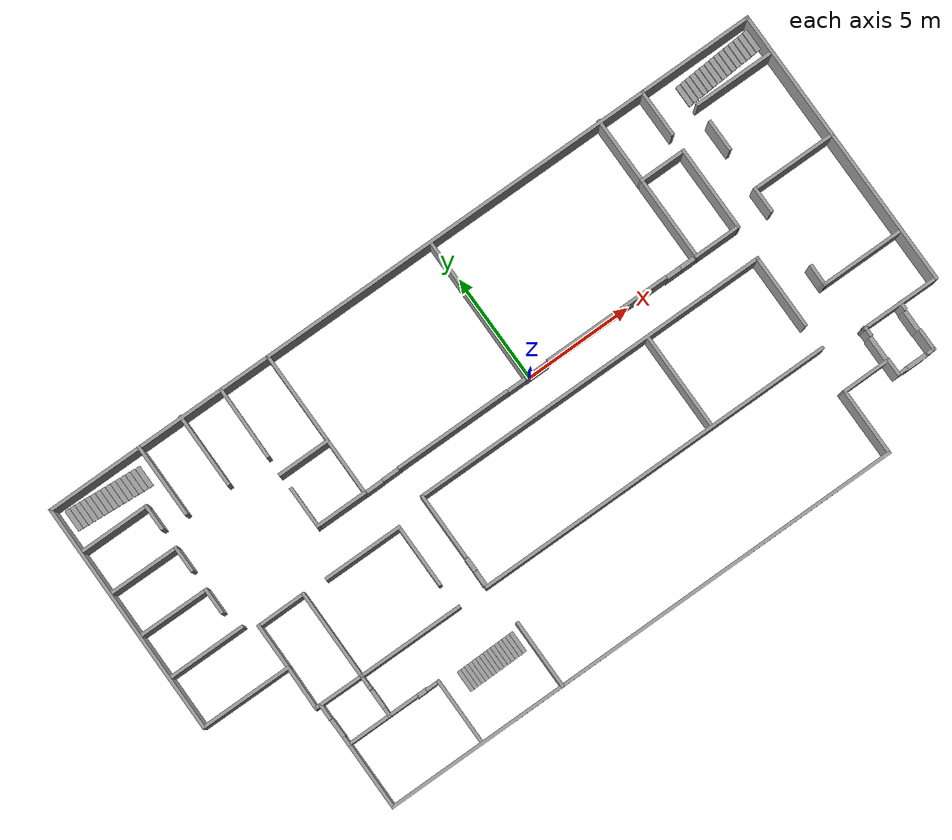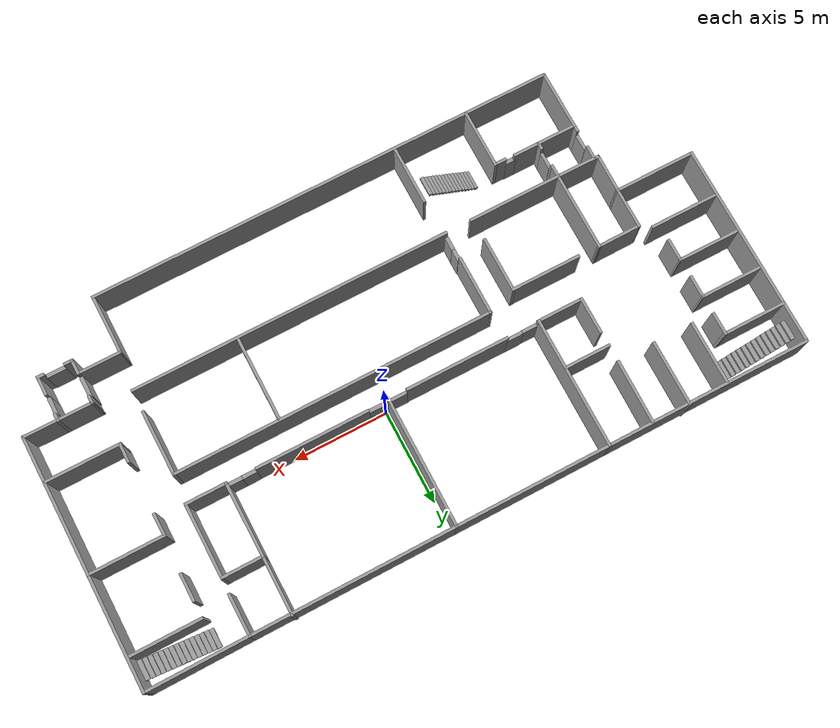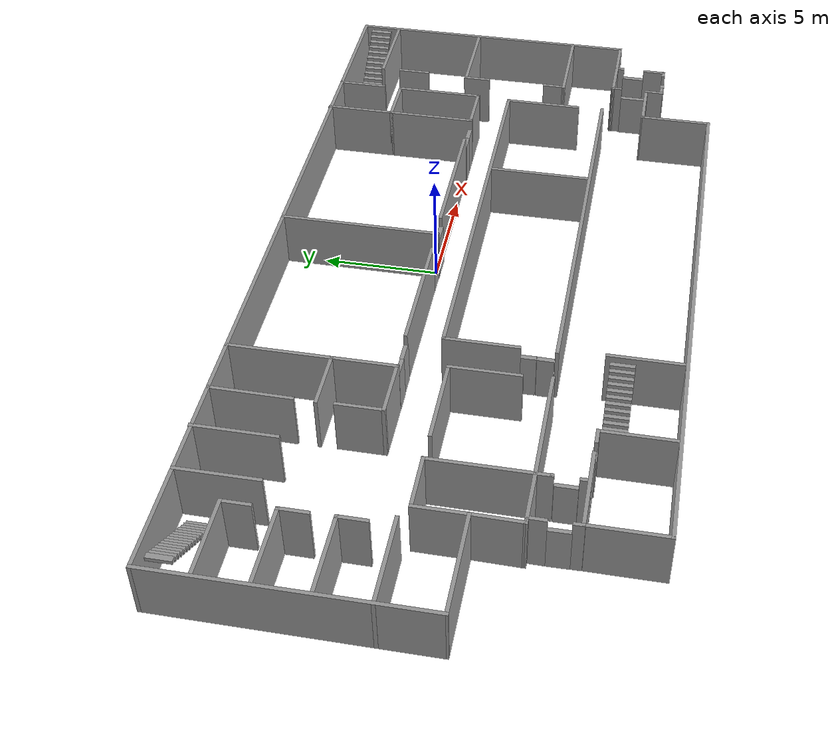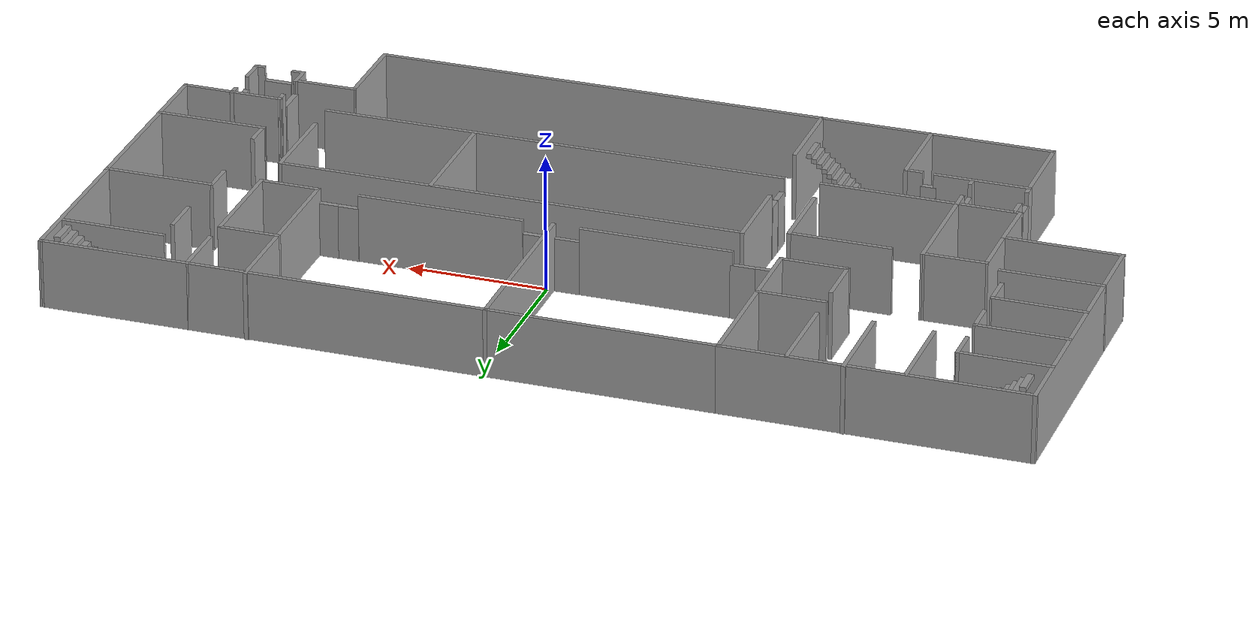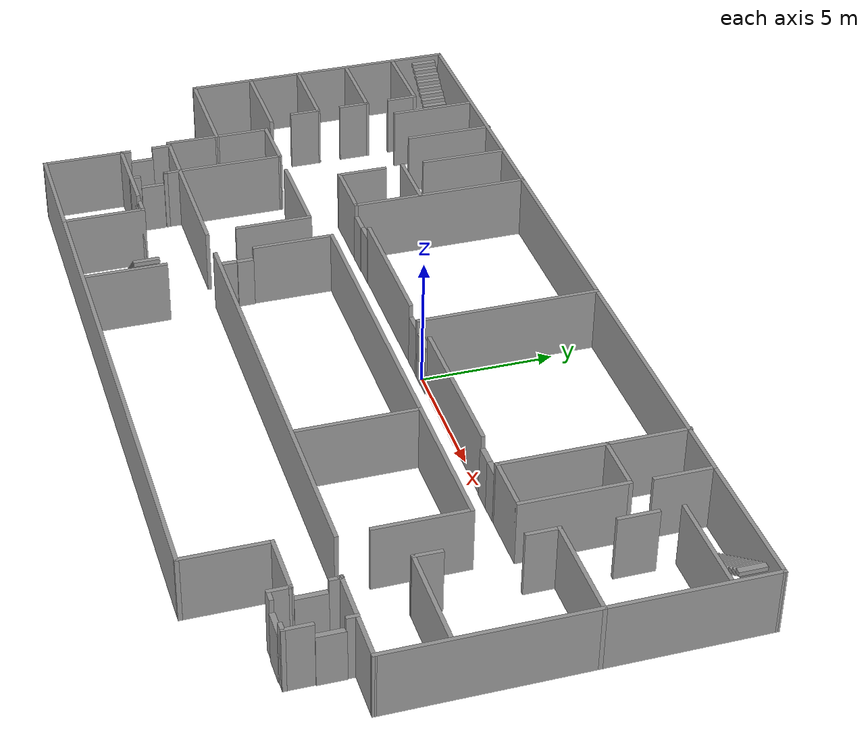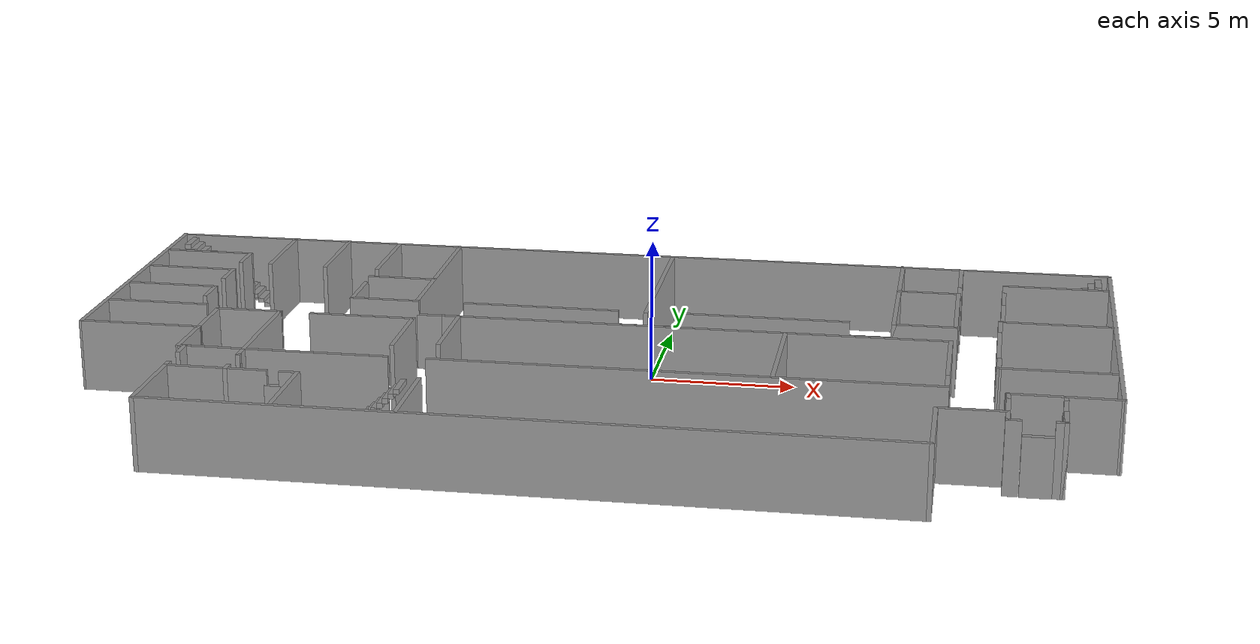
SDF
<?xml version='1.0'?>
<sdf version='1.6'>
  <model name='Devon1st'>
    <pose frame=''>-1.69597 -2.20458 0 0 -0 0</pose>
    <link name='Door_0'>
      <collision name='Door_0_Collision'>
        <geometry>
          <box>
            <size>0.9 0.17 2</size>
          </box>
        </geometry>
        <pose frame=''>0 0 1 0 -0 0</pose>
      </collision>
      <visual name='Door_0_Visual'>
        <pose frame=''>0 0 1 0 -0 0</pose>
        <geometry>
          <box>
            <size>0.9 0.17 2</size>
          </box>
        </geometry>
        <material>
          <script>
            <uri>file://media/materials/scripts/gazebo.material</uri>
            <name>Gazebo/Grey</name>
          </script>
        </material>
      </visual>
      <pose frame=''>0.962479 2.12819 0 0 -0 0</pose>
    </link>
    <link name='Door_1'>
      <collision name='Door_1_Collision'>
        <geometry>
          <box>
            <size>1.01304 0.2 2</size>
          </box>
        </geometry>
        <pose frame=''>0 0 1 0 -0 0</pose>
      </collision>
      <visual name='Door_1_Visual'>
        <pose frame=''>0 0 1 0 -0 0</pose>
        <geometry>
          <box>
            <size>1.01304 0.2 2</size>
          </box>
        </geometry>
        <material>
          <script>
            <uri>file://media/materials/scripts/gazebo.material</uri>
            <name>Gazebo/Grey</name>
          </script>
        </material>
      </visual>
      <pose frame=''>2.05919 2.13031 0 0 -0 0</pose>
    </link>
    <link name='Door_10'>
      <collision name='Door_10_Collision'>
        <geometry>
          <box>
            <size>0.9 0.17 2</size>
          </box>
        </geometry>
        <pose frame=''>0 0 1 0 -0 0</pose>
      </collision>
      <visual name='Door_10_Visual'>
        <pose frame=''>0 0 1 0 -0 0</pose>
        <geometry>
          <box>
            <size>0.9 0.17 2</size>
          </box>
        </geometry>
        <material>
          <script>
            <uri>file://media/materials/scripts/gazebo.material</uri>
            <name>Gazebo/Grey</name>
          </script>
        </material>
      </visual>
      <pose frame=''>-11.095 -5.06555 0 0 0 -1.57113</pose>
    </link>
    <link name='Door_11'>
      <collision name='Door_11_Collision'>
        <geometry>
          <box>
            <size>1.12 0.2 2</size>
          </box>
        </geometry>
        <pose frame=''>0 0 1 0 -0 0</pose>
      </collision>
      <visual name='Door_11_Visual'>
        <pose frame=''>0 0 1 0 -0 0</pose>
        <geometry>
          <box>
            <size>1.12 0.2 2</size>
          </box>
        </geometry>
        <material>
          <script>
            <uri>file://media/materials/scripts/gazebo.material</uri>
            <name>Gazebo/Grey</name>
          </script>
        </material>
      </visual>
      <pose frame=''>13.9457 -5.24793 0 0 -0 1.5708</pose>
    </link>
    <link name='Door_12'>
      <collision name='Door_12_Collision'>
        <geometry>
          <box>
            <size>1.0094 0.2 2</size>
          </box>
        </geometry>
        <pose frame=''>0 0 1 0 -0 0</pose>
      </collision>
      <visual name='Door_12_Visual'>
        <pose frame=''>0 0 1 0 -0 0</pose>
        <geometry>
          <box>
            <size>1.0094 0.2 2</size>
          </box>
        </geometry>
        <material>
          <script>
            <uri>file://media/materials/scripts/gazebo.material</uri>
            <name>Gazebo/Grey</name>
          </script>
        </material>
      </visual>
      <pose frame=''>15.7353 -5.11263 0 0 -0 1.56332</pose>
    </link>
    <link name='Door_13'>
      <collision name='Door_13_Collision'>
        <geometry>
          <box>
            <size>1.01 0.2 2</size>
          </box>
        </geometry>
        <pose frame=''>0 0 1 0 -0 0</pose>
      </collision>
      <visual name='Door_13_Visual'>
        <pose frame=''>0 0 1 0 -0 0</pose>
        <geometry>
          <box>
            <size>1.01 0.2 2</size>
          </box>
        </geometry>
        <material>
          <script>
            <uri>file://media/materials/scripts/gazebo.material</uri>
            <name>Gazebo/Grey</name>
          </script>
        </material>
      </visual>
      <pose frame=''>14.8957 -6.60293 0 0 -0 0</pose>
    </link>
    <link name='Door_2'>
      <collision name='Door_2_Collision'>
        <geometry>
          <box>
            <size>0.9 0.17 2</size>
          </box>
        </geometry>
        <pose frame=''>0 0 1 0 -0 0</pose>
      </collision>
      <visual name='Door_2_Visual'>
        <pose frame=''>0 0 1 0 -0 0</pose>
        <geometry>
          <box>
            <size>0.9 0.17 2</size>
          </box>
        </geometry>
        <material>
          <script>
            <uri>file://media/materials/scripts/gazebo.material</uri>
            <name>Gazebo/Grey</name>
          </script>
        </material>
      </visual>
      <pose frame=''>-6.22882 2.1021 0 0 -0 0</pose>
    </link>
    <link name='Door_3'>
      <collision name='Door_3_Collision'>
        <geometry>
          <box>
            <size>0.9 0.17 2</size>
          </box>
        </geometry>
        <pose frame=''>0 0 1 0 -0 0</pose>
      </collision>
      <visual name='Door_3_Visual'>
        <pose frame=''>0 0 1 0 -0 0</pose>
        <geometry>
          <box>
            <size>0.9 0.17 2</size>
          </box>
        </geometry>
        <material>
          <script>
            <uri>file://media/materials/scripts/gazebo.material</uri>
            <name>Gazebo/Grey</name>
          </script>
        </material>
      </visual>
      <pose frame=''>-5.34187 2.1195 0 0 -0 0</pose>
    </link>
    <link name='Door_4'>
      <collision name='Door_4_Collision'>
        <geometry>
          <box>
            <size>0.556948 0.2 2</size>
          </box>
        </geometry>
        <pose frame=''>0 0 1 0 -0 0</pose>
      </collision>
      <visual name='Door_4_Visual'>
        <pose frame=''>0 0 1 0 -0 0</pose>
        <geometry>
          <box>
            <size>0.556948 0.2 2</size>
          </box>
        </geometry>
        <material>
          <script>
            <uri>file://media/materials/scripts/gazebo.material</uri>
            <name>Gazebo/Grey</name>
          </script>
        </material>
      </visual>
      <pose frame=''>-9.50821 -5.91025 0 0 -0 0</pose>
    </link>
    <link name='Door_5'>
      <collision name='Door_5_Collision'>
        <geometry>
          <box>
            <size>0.745 0.2 2</size>
          </box>
        </geometry>
        <pose frame=''>0 0 1 0 -0 0</pose>
      </collision>
      <visual name='Door_5_Visual'>
        <pose frame=''>0 0 1 0 -0 0</pose>
        <geometry>
          <box>
            <size>0.745 0.2 2</size>
          </box>
        </geometry>
        <material>
          <script>
            <uri>file://media/materials/scripts/gazebo.material</uri>
            <name>Gazebo/Grey</name>
          </script>
        </material>
      </visual>
      <pose frame=''>8.90588 2.1621 0 0 -0 0</pose>
    </link>
    <link name='Door_6'>
      <collision name='Door_6_Collision'>
        <geometry>
          <box>
            <size>0.71 0.2 2</size>
          </box>
        </geometry>
        <pose frame=''>0 0 1 0 -0 0</pose>
      </collision>
      <visual name='Door_6_Visual'>
        <pose frame=''>0 0 1 0 -0 0</pose>
        <geometry>
          <box>
            <size>0.71 0.2 2</size>
          </box>
        </geometry>
        <material>
          <script>
            <uri>file://media/materials/scripts/gazebo.material</uri>
            <name>Gazebo/Grey</name>
          </script>
        </material>
      </visual>
      <pose frame=''>9.63338 2.1621 0 0 -0 0</pose>
    </link>
    <link name='Door_7'>
      <collision name='Door_7_Collision'>
        <geometry>
          <box>
            <size>0.631949 0.2 2</size>
          </box>
        </geometry>
        <pose frame=''>0 0 1 0 -0 0</pose>
      </collision>
      <visual name='Door_7_Visual'>
        <pose frame=''>0 0 1 0 -0 0</pose>
        <geometry>
          <box>
            <size>0.631949 0.2 2</size>
          </box>
        </geometry>
        <material>
          <script>
            <uri>file://media/materials/scripts/gazebo.material</uri>
            <name>Gazebo/Grey</name>
          </script>
        </material>
      </visual>
      <pose frame=''>-4.82459 -2.7964 0 0 0 -1.56264</pose>
    </link>
    <link name='Door_8'>
      <collision name='Door_8_Collision'>
        <geometry>
          <box>
            <size>0.695848 0.2 2</size>
          </box>
        </geometry>
        <pose frame=''>0 0 1 0 -0 0</pose>
      </collision>
      <visual name='Door_8_Visual'>
        <pose frame=''>0 0 1 0 -0 0</pose>
        <geometry>
          <box>
            <size>0.695848 0.2 2</size>
          </box>
        </geometry>
        <material>
          <script>
            <uri>file://media/materials/scripts/gazebo.material</uri>
            <name>Gazebo/Grey</name>
          </script>
        </material>
      </visual>
      <pose frame=''>-4.83152 -3.47647 0 0 0 -1.58327</pose>
    </link>
    <link name='Door_9'>
      <collision name='Door_9_Collision'>
        <geometry>
          <box>
            <size>0.9 0.17 2</size>
          </box>
        </geometry>
        <pose frame=''>0 0 1 0 -0 0</pose>
      </collision>
      <visual name='Door_9_Visual'>
        <pose frame=''>0 0 1 0 -0 0</pose>
        <geometry>
          <box>
            <size>0.9 0.17 2</size>
          </box>
        </geometry>
        <material>
          <script>
            <uri>file://media/materials/scripts/gazebo.material</uri>
            <name>Gazebo/Grey</name>
          </script>
        </material>
      </visual>
      <pose frame=''>-13.1241 -5.08705 0 0 0 -1.55889</pose>
    </link>
    <link name='Stairs_2'>
      <visual name='Stairs_2_Visual_0'>
        <pose frame=''>-7.74491 -6.50403 0.083333 0 -0 1.5708</pose>
        <geometry>
          <box>
            <size>1 0.187333 0.166667</size>
          </box>
        </geometry>
        <material>
          <script>
            <uri>file://media/materials/scripts/gazebo.material</uri>
            <name>Gazebo/Grey</name>
          </script>
          <ambient>1 1 1 1</ambient>
        </material>
      </visual>
      <collision name='Stairs_2_Collision_0'>
        <geometry>
          <box>
            <size>1 0.187333 0.166667</size>
          </box>
        </geometry>
        <pose frame=''>-7.74491 -6.50403 0.083333 0 -0 1.5708</pose>
      </collision>
      <visual name='Stairs_2_Visual_1'>
        <pose frame=''>-7.55758 -6.50403 0.25 0 -0 1.5708</pose>
        <geometry>
          <box>
            <size>1 0.187333 0.166667</size>
          </box>
        </geometry>
        <material>
          <script>
            <uri>file://media/materials/scripts/gazebo.material</uri>
            <name>Gazebo/Grey</name>
          </script>
          <ambient>1 1 1 1</ambient>
        </material>
      </visual>
      <collision name='Stairs_2_Collision_1'>
        <geometry>
          <box>
            <size>1 0.187333 0.166667</size>
          </box>
        </geometry>
        <pose frame=''>-7.55758 -6.50403 0.25 0 -0 1.5708</pose>
      </collision>
      <visual name='Stairs_2_Visual_2'>
        <pose frame=''>-7.37024 -6.50403 0.416667 0 -0 1.5708</pose>
        <geometry>
          <box>
            <size>1 0.187333 0.166667</size>
          </box>
        </geometry>
        <material>
          <script>
            <uri>file://media/materials/scripts/gazebo.material</uri>
            <name>Gazebo/Grey</name>
          </script>
          <ambient>1 1 1 1</ambient>
        </material>
      </visual>
      <collision name='Stairs_2_Collision_2'>
        <geometry>
          <box>
            <size>1 0.187333 0.166667</size>
          </box>
        </geometry>
        <pose frame=''>-7.37024 -6.50403 0.416667 0 -0 1.5708</pose>
      </collision>
      <visual name='Stairs_2_Visual_3'>
        <pose frame=''>-7.18291 -6.50403 0.583333 0 -0 1.5708</pose>
        <geometry>
          <box>
            <size>1 0.187333 0.166667</size>
          </box>
        </geometry>
        <material>
          <script>
            <uri>file://media/materials/scripts/gazebo.material</uri>
            <name>Gazebo/Grey</name>
          </script>
          <ambient>1 1 1 1</ambient>
        </material>
      </visual>
      <collision name='Stairs_2_Collision_3'>
        <geometry>
          <box>
            <size>1 0.187333 0.166667</size>
          </box>
        </geometry>
        <pose frame=''>-7.18291 -6.50403 0.583333 0 -0 1.5708</pose>
      </collision>
      <visual name='Stairs_2_Visual_4'>
        <pose frame=''>-6.99558 -6.50403 0.75 0 -0 1.5708</pose>
        <geometry>
          <box>
            <size>1 0.187333 0.166667</size>
          </box>
        </geometry>
        <material>
          <script>
            <uri>file://media/materials/scripts/gazebo.material</uri>
            <name>Gazebo/Grey</name>
          </script>
          <ambient>1 1 1 1</ambient>
        </material>
      </visual>
      <collision name='Stairs_2_Collision_4'>
        <geometry>
          <box>
            <size>1 0.187333 0.166667</size>
          </box>
        </geometry>
        <pose frame=''>-6.99558 -6.50403 0.75 0 -0 1.5708</pose>
      </collision>
      <visual name='Stairs_2_Visual_5'>
        <pose frame=''>-6.80824 -6.50403 0.916667 0 -0 1.5708</pose>
        <geometry>
          <box>
            <size>1 0.187333 0.166667</size>
          </box>
        </geometry>
        <material>
          <script>
            <uri>file://media/materials/scripts/gazebo.material</uri>
            <name>Gazebo/Grey</name>
          </script>
          <ambient>1 1 1 1</ambient>
        </material>
      </visual>
      <collision name='Stairs_2_Collision_5'>
        <geometry>
          <box>
            <size>1 0.187333 0.166667</size>
          </box>
        </geometry>
        <pose frame=''>-6.80824 -6.50403 0.916667 0 -0 1.5708</pose>
      </collision>
      <visual name='Stairs_2_Visual_6'>
        <pose frame=''>-6.62091 -6.50403 1.08333 0 -0 1.5708</pose>
        <geometry>
          <box>
            <size>1 0.187333 0.166667</size>
          </box>
        </geometry>
        <material>
          <script>
            <uri>file://media/materials/scripts/gazebo.material</uri>
            <name>Gazebo/Grey</name>
          </script>
          <ambient>1 1 1 1</ambient>
        </material>
      </visual>
      <collision name='Stairs_2_Collision_6'>
        <geometry>
          <box>
            <size>1 0.187333 0.166667</size>
          </box>
        </geometry>
        <pose frame=''>-6.62091 -6.50403 1.08333 0 -0 1.5708</pose>
      </collision>
      <visual name='Stairs_2_Visual_7'>
        <pose frame=''>-6.43358 -6.50403 1.25 0 -0 1.5708</pose>
        <geometry>
          <box>
            <size>1 0.187333 0.166667</size>
          </box>
        </geometry>
        <material>
          <script>
            <uri>file://media/materials/scripts/gazebo.material</uri>
            <name>Gazebo/Grey</name>
          </script>
          <ambient>1 1 1 1</ambient>
        </material>
      </visual>
      <collision name='Stairs_2_Collision_7'>
        <geometry>
          <box>
            <size>1 0.187333 0.166667</size>
          </box>
        </geometry>
        <pose frame=''>-6.43358 -6.50403 1.25 0 -0 1.5708</pose>
      </collision>
      <visual name='Stairs_2_Visual_8'>
        <pose frame=''>-6.24624 -6.50403 1.41667 0 -0 1.5708</pose>
        <geometry>
          <box>
            <size>1 0.187333 0.166667</size>
          </box>
        </geometry>
        <material>
          <script>
            <uri>file://media/materials/scripts/gazebo.material</uri>
            <name>Gazebo/Grey</name>
          </script>
          <ambient>1 1 1 1</ambient>
        </material>
      </visual>
      <collision name='Stairs_2_Collision_8'>
        <geometry>
          <box>
            <size>1 0.187333 0.166667</size>
          </box>
        </geometry>
        <pose frame=''>-6.24624 -6.50403 1.41667 0 -0 1.5708</pose>
      </collision>
      <visual name='Stairs_2_Visual_9'>
        <pose frame=''>-6.05891 -6.50403 1.58333 0 -0 1.5708</pose>
        <geometry>
          <box>
            <size>1 0.187333 0.166667</size>
          </box>
        </geometry>
        <material>
          <script>
            <uri>file://media/materials/scripts/gazebo.material</uri>
            <name>Gazebo/Grey</name>
          </script>
          <ambient>1 1 1 1</ambient>
        </material>
      </visual>
      <collision name='Stairs_2_Collision_9'>
        <geometry>
          <box>
            <size>1 0.187333 0.166667</size>
          </box>
        </geometry>
        <pose frame=''>-6.05891 -6.50403 1.58333 0 -0 1.5708</pose>
      </collision>
      <visual name='Stairs_2_Visual_10'>
        <pose frame=''>-5.87158 -6.50403 1.75 0 -0 1.5708</pose>
        <geometry>
          <box>
            <size>1 0.187333 0.166667</size>
          </box>
        </geometry>
        <material>
          <script>
            <uri>file://media/materials/scripts/gazebo.material</uri>
            <name>Gazebo/Grey</name>
          </script>
          <ambient>1 1 1 1</ambient>
        </material>
      </visual>
      <collision name='Stairs_2_Collision_10'>
        <geometry>
          <box>
            <size>1 0.187333 0.166667</size>
          </box>
        </geometry>
        <pose frame=''>-5.87158 -6.50403 1.75 0 -0 1.5708</pose>
      </collision>
      <visual name='Stairs_2_Visual_11'>
        <pose frame=''>-5.68424 -6.50403 1.91667 0 -0 1.5708</pose>
        <geometry>
          <box>
            <size>1 0.187333 0.166667</size>
          </box>
        </geometry>
        <material>
          <script>
            <uri>file://media/materials/scripts/gazebo.material</uri>
            <name>Gazebo/Grey</name>
          </script>
          <ambient>1 1 1 1</ambient>
        </material>
      </visual>
      <collision name='Stairs_2_Collision_11'>
        <geometry>
          <box>
            <size>1 0.187333 0.166667</size>
          </box>
        </geometry>
        <pose frame=''>-5.68424 -6.50403 1.91667 0 -0 1.5708</pose>
      </collision>
      <visual name='Stairs_2_Visual_12'>
        <pose frame=''>-5.49691 -6.50403 2.08333 0 -0 1.5708</pose>
        <geometry>
          <box>
            <size>1 0.187333 0.166667</size>
          </box>
        </geometry>
        <material>
          <script>
            <uri>file://media/materials/scripts/gazebo.material</uri>
            <name>Gazebo/Grey</name>
          </script>
          <ambient>1 1 1 1</ambient>
        </material>
      </visual>
      <collision name='Stairs_2_Collision_12'>
        <geometry>
          <box>
            <size>1 0.187333 0.166667</size>
          </box>
        </geometry>
        <pose frame=''>-5.49691 -6.50403 2.08333 0 -0 1.5708</pose>
      </collision>
      <visual name='Stairs_2_Visual_13'>
        <pose frame=''>-5.30958 -6.50403 2.25 0 -0 1.5708</pose>
        <geometry>
          <box>
            <size>1 0.187333 0.166667</size>
          </box>
        </geometry>
        <material>
          <script>
            <uri>file://media/materials/scripts/gazebo.material</uri>
            <name>Gazebo/Grey</name>
          </script>
          <ambient>1 1 1 1</ambient>
        </material>
      </visual>
      <collision name='Stairs_2_Collision_13'>
        <geometry>
          <box>
            <size>1 0.187333 0.166667</size>
          </box>
        </geometry>
        <pose frame=''>-5.30958 -6.50403 2.25 0 -0 1.5708</pose>
      </collision>
      <visual name='Stairs_2_Visual_14'>
        <pose frame=''>-5.12224 -6.50403 2.41667 0 -0 1.5708</pose>
        <geometry>
          <box>
            <size>1 0.187333 0.166667</size>
          </box>
        </geometry>
        <material>
          <script>
            <uri>file://media/materials/scripts/gazebo.material</uri>
            <name>Gazebo/Grey</name>
          </script>
          <ambient>1 1 1 1</ambient>
        </material>
      </visual>
      <collision name='Stairs_2_Collision_14'>
        <geometry>
          <box>
            <size>1 0.187333 0.166667</size>
          </box>
        </geometry>
        <pose frame=''>-5.12224 -6.50403 2.41667 0 -0 1.5708</pose>
      </collision>
    </link>
    <link name='Stairs_3'>
      <visual name='Stairs_3_Visual_0'>
        <pose frame=''>13.8125 8.06468 0.083333 0 -0 1.5708</pose>
        <geometry>
          <box>
            <size>1 0.233333 0.166667</size>
          </box>
        </geometry>
        <material>
          <script>
            <uri>file://media/materials/scripts/gazebo.material</uri>
            <name>Gazebo/Grey</name>
          </script>
          <ambient>1 1 1 1</ambient>
        </material>
      </visual>
      <collision name='Stairs_3_Collision_0'>
        <geometry>
          <box>
            <size>1 0.233333 0.166667</size>
          </box>
        </geometry>
        <pose frame=''>13.8125 8.06468 0.083333 0 -0 1.5708</pose>
      </collision>
      <visual name='Stairs_3_Visual_1'>
        <pose frame=''>14.0458 8.06468 0.25 0 -0 1.5708</pose>
        <geometry>
          <box>
            <size>1 0.233333 0.166667</size>
          </box>
        </geometry>
        <material>
          <script>
            <uri>file://media/materials/scripts/gazebo.material</uri>
            <name>Gazebo/Grey</name>
          </script>
          <ambient>1 1 1 1</ambient>
        </material>
      </visual>
      <collision name='Stairs_3_Collision_1'>
        <geometry>
          <box>
            <size>1 0.233333 0.166667</size>
          </box>
        </geometry>
        <pose frame=''>14.0458 8.06468 0.25 0 -0 1.5708</pose>
      </collision>
      <visual name='Stairs_3_Visual_2'>
        <pose frame=''>14.2792 8.06468 0.416667 0 -0 1.5708</pose>
        <geometry>
          <box>
            <size>1 0.233333 0.166667</size>
          </box>
        </geometry>
        <material>
          <script>
            <uri>file://media/materials/scripts/gazebo.material</uri>
            <name>Gazebo/Grey</name>
          </script>
          <ambient>1 1 1 1</ambient>
        </material>
      </visual>
      <collision name='Stairs_3_Collision_2'>
        <geometry>
          <box>
            <size>1 0.233333 0.166667</size>
          </box>
        </geometry>
        <pose frame=''>14.2792 8.06468 0.416667 0 -0 1.5708</pose>
      </collision>
      <visual name='Stairs_3_Visual_3'>
        <pose frame=''>14.5125 8.06468 0.583333 0 -0 1.5708</pose>
        <geometry>
          <box>
            <size>1 0.233333 0.166667</size>
          </box>
        </geometry>
        <material>
          <script>
            <uri>file://media/materials/scripts/gazebo.material</uri>
            <name>Gazebo/Grey</name>
          </script>
          <ambient>1 1 1 1</ambient>
        </material>
      </visual>
      <collision name='Stairs_3_Collision_3'>
        <geometry>
          <box>
            <size>1 0.233333 0.166667</size>
          </box>
        </geometry>
        <pose frame=''>14.5125 8.06468 0.583333 0 -0 1.5708</pose>
      </collision>
      <visual name='Stairs_3_Visual_4'>
        <pose frame=''>14.7458 8.06468 0.75 0 -0 1.5708</pose>
        <geometry>
          <box>
            <size>1 0.233333 0.166667</size>
          </box>
        </geometry>
        <material>
          <script>
            <uri>file://media/materials/scripts/gazebo.material</uri>
            <name>Gazebo/Grey</name>
          </script>
          <ambient>1 1 1 1</ambient>
        </material>
      </visual>
      <collision name='Stairs_3_Collision_4'>
        <geometry>
          <box>
            <size>1 0.233333 0.166667</size>
          </box>
        </geometry>
        <pose frame=''>14.7458 8.06468 0.75 0 -0 1.5708</pose>
      </collision>
      <visual name='Stairs_3_Visual_5'>
        <pose frame=''>14.9792 8.06468 0.916667 0 -0 1.5708</pose>
        <geometry>
          <box>
            <size>1 0.233333 0.166667</size>
          </box>
        </geometry>
        <material>
          <script>
            <uri>file://media/materials/scripts/gazebo.material</uri>
            <name>Gazebo/Grey</name>
          </script>
          <ambient>1 1 1 1</ambient>
        </material>
      </visual>
      <collision name='Stairs_3_Collision_5'>
        <geometry>
          <box>
            <size>1 0.233333 0.166667</size>
          </box>
        </geometry>
        <pose frame=''>14.9792 8.06468 0.916667 0 -0 1.5708</pose>
      </collision>
      <visual name='Stairs_3_Visual_6'>
        <pose frame=''>15.2125 8.06468 1.08333 0 -0 1.5708</pose>
        <geometry>
          <box>
            <size>1 0.233333 0.166667</size>
          </box>
        </geometry>
        <material>
          <script>
            <uri>file://media/materials/scripts/gazebo.material</uri>
            <name>Gazebo/Grey</name>
          </script>
          <ambient>1 1 1 1</ambient>
        </material>
      </visual>
      <collision name='Stairs_3_Collision_6'>
        <geometry>
          <box>
            <size>1 0.233333 0.166667</size>
          </box>
        </geometry>
        <pose frame=''>15.2125 8.06468 1.08333 0 -0 1.5708</pose>
      </collision>
      <visual name='Stairs_3_Visual_7'>
        <pose frame=''>15.4458 8.06468 1.25 0 -0 1.5708</pose>
        <geometry>
          <box>
            <size>1 0.233333 0.166667</size>
          </box>
        </geometry>
        <material>
          <script>
            <uri>file://media/materials/scripts/gazebo.material</uri>
            <name>Gazebo/Grey</name>
          </script>
          <ambient>1 1 1 1</ambient>
        </material>
      </visual>
      <collision name='Stairs_3_Collision_7'>
        <geometry>
          <box>
            <size>1 0.233333 0.166667</size>
          </box>
        </geometry>
        <pose frame=''>15.4458 8.06468 1.25 0 -0 1.5708</pose>
      </collision>
      <visual name='Stairs_3_Visual_8'>
        <pose frame=''>15.6792 8.06468 1.41667 0 -0 1.5708</pose>
        <geometry>
          <box>
            <size>1 0.233333 0.166667</size>
          </box>
        </geometry>
        <material>
          <script>
            <uri>file://media/materials/scripts/gazebo.material</uri>
            <name>Gazebo/Grey</name>
          </script>
          <ambient>1 1 1 1</ambient>
        </material>
      </visual>
      <collision name='Stairs_3_Collision_8'>
        <geometry>
          <box>
            <size>1 0.233333 0.166667</size>
          </box>
        </geometry>
        <pose frame=''>15.6792 8.06468 1.41667 0 -0 1.5708</pose>
      </collision>
      <visual name='Stairs_3_Visual_9'>
        <pose frame=''>15.9125 8.06468 1.58333 0 -0 1.5708</pose>
        <geometry>
          <box>
            <size>1 0.233333 0.166667</size>
          </box>
        </geometry>
        <material>
          <script>
            <uri>file://media/materials/scripts/gazebo.material</uri>
            <name>Gazebo/Grey</name>
          </script>
          <ambient>1 1 1 1</ambient>
        </material>
      </visual>
      <collision name='Stairs_3_Collision_9'>
        <geometry>
          <box>
            <size>1 0.233333 0.166667</size>
          </box>
        </geometry>
        <pose frame=''>15.9125 8.06468 1.58333 0 -0 1.5708</pose>
      </collision>
      <visual name='Stairs_3_Visual_10'>
        <pose frame=''>16.1458 8.06468 1.75 0 -0 1.5708</pose>
        <geometry>
          <box>
            <size>1 0.233333 0.166667</size>
          </box>
        </geometry>
        <material>
          <script>
            <uri>file://media/materials/scripts/gazebo.material</uri>
            <name>Gazebo/Grey</name>
          </script>
          <ambient>1 1 1 1</ambient>
        </material>
      </visual>
      <collision name='Stairs_3_Collision_10'>
        <geometry>
          <box>
            <size>1 0.233333 0.166667</size>
          </box>
        </geometry>
        <pose frame=''>16.1458 8.06468 1.75 0 -0 1.5708</pose>
      </collision>
      <visual name='Stairs_3_Visual_11'>
        <pose frame=''>16.3792 8.06468 1.91667 0 -0 1.5708</pose>
        <geometry>
          <box>
            <size>1 0.233333 0.166667</size>
          </box>
        </geometry>
        <material>
          <script>
            <uri>file://media/materials/scripts/gazebo.material</uri>
            <name>Gazebo/Grey</name>
          </script>
          <ambient>1 1 1 1</ambient>
        </material>
      </visual>
      <collision name='Stairs_3_Collision_11'>
        <geometry>
          <box>
            <size>1 0.233333 0.166667</size>
          </box>
        </geometry>
        <pose frame=''>16.3792 8.06468 1.91667 0 -0 1.5708</pose>
      </collision>
      <visual name='Stairs_3_Visual_12'>
        <pose frame=''>16.6125 8.06468 2.08333 0 -0 1.5708</pose>
        <geometry>
          <box>
            <size>1 0.233333 0.166667</size>
          </box>
        </geometry>
        <material>
          <script>
            <uri>file://media/materials/scripts/gazebo.material</uri>
            <name>Gazebo/Grey</name>
          </script>
          <ambient>1 1 1 1</ambient>
        </material>
      </visual>
      <collision name='Stairs_3_Collision_12'>
        <geometry>
          <box>
            <size>1 0.233333 0.166667</size>
          </box>
        </geometry>
        <pose frame=''>16.6125 8.06468 2.08333 0 -0 1.5708</pose>
      </collision>
      <visual name='Stairs_3_Visual_13'>
        <pose frame=''>16.8458 8.06468 2.25 0 -0 1.5708</pose>
        <geometry>
          <box>
            <size>1 0.233333 0.166667</size>
          </box>
        </geometry>
        <material>
          <script>
            <uri>file://media/materials/scripts/gazebo.material</uri>
            <name>Gazebo/Grey</name>
          </script>
          <ambient>1 1 1 1</ambient>
        </material>
      </visual>
      <collision name='Stairs_3_Collision_13'>
        <geometry>
          <box>
            <size>1 0.233333 0.166667</size>
          </box>
        </geometry>
        <pose frame=''>16.8458 8.06468 2.25 0 -0 1.5708</pose>
      </collision>
      <visual name='Stairs_3_Visual_14'>
        <pose frame=''>17.0792 8.06468 2.41667 0 -0 1.5708</pose>
        <geometry>
          <box>
            <size>1 0.233333 0.166667</size>
          </box>
        </geometry>
        <material>
          <script>
            <uri>file://media/materials/scripts/gazebo.material</uri>
            <name>Gazebo/Grey</name>
          </script>
          <ambient>1 1 1 1</ambient>
        </material>
      </visual>
      <collision name='Stairs_3_Collision_14'>
        <geometry>
          <box>
            <size>1 0.233333 0.166667</size>
          </box>
        </geometry>
        <pose frame=''>17.0792 8.06468 2.41667 0 -0 1.5708</pose>
      </collision>
    </link>
    <link name='Stairs_4'>
      <visual name='Stairs_4_Visual_0'>
        <pose frame=''>-13.7119 8.07177 0.083333 0 -0 -1.5708</pose>
        <geometry>
          <box>
            <size>1 0.233333 0.166667</size>
          </box>
        </geometry>
        <material>
          <script>
            <uri>file://media/materials/scripts/gazebo.material</uri>
            <name>Gazebo/Grey</name>
          </script>
          <ambient>1 1 1 1</ambient>
        </material>
      </visual>
      <collision name='Stairs_4_Collision_0'>
        <geometry>
          <box>
            <size>1 0.233333 0.166667</size>
          </box>
        </geometry>
        <pose frame=''>-13.7119 8.07177 0.083333 0 -0 -1.5708</pose>
      </collision>
      <visual name='Stairs_4_Visual_1'>
        <pose frame=''>-13.9452 8.07177 0.25 0 -0 -1.5708</pose>
        <geometry>
          <box>
            <size>1 0.233333 0.166667</size>
          </box>
        </geometry>
        <material>
          <script>
            <uri>file://media/materials/scripts/gazebo.material</uri>
            <name>Gazebo/Grey</name>
          </script>
          <ambient>1 1 1 1</ambient>
        </material>
      </visual>
      <collision name='Stairs_4_Collision_1'>
        <geometry>
          <box>
            <size>1 0.233333 0.166667</size>
          </box>
        </geometry>
        <pose frame=''>-13.9452 8.07177 0.25 0 -0 -1.5708</pose>
      </collision>
      <visual name='Stairs_4_Visual_2'>
        <pose frame=''>-14.1786 8.07177 0.416667 0 -0 -1.5708</pose>
        <geometry>
          <box>
            <size>1 0.233333 0.166667</size>
          </box>
        </geometry>
        <material>
          <script>
            <uri>file://media/materials/scripts/gazebo.material</uri>
            <name>Gazebo/Grey</name>
          </script>
          <ambient>1 1 1 1</ambient>
        </material>
      </visual>
      <collision name='Stairs_4_Collision_2'>
        <geometry>
          <box>
            <size>1 0.233333 0.166667</size>
          </box>
        </geometry>
        <pose frame=''>-14.1786 8.07177 0.416667 0 -0 -1.5708</pose>
      </collision>
      <visual name='Stairs_4_Visual_3'>
        <pose frame=''>-14.4119 8.07177 0.583333 0 -0 -1.5708</pose>
        <geometry>
          <box>
            <size>1 0.233333 0.166667</size>
          </box>
        </geometry>
        <material>
          <script>
            <uri>file://media/materials/scripts/gazebo.material</uri>
            <name>Gazebo/Grey</name>
          </script>
          <ambient>1 1 1 1</ambient>
        </material>
      </visual>
      <collision name='Stairs_4_Collision_3'>
        <geometry>
          <box>
            <size>1 0.233333 0.166667</size>
          </box>
        </geometry>
        <pose frame=''>-14.4119 8.07177 0.583333 0 -0 -1.5708</pose>
      </collision>
      <visual name='Stairs_4_Visual_4'>
        <pose frame=''>-14.6452 8.07177 0.75 0 -0 -1.5708</pose>
        <geometry>
          <box>
            <size>1 0.233333 0.166667</size>
          </box>
        </geometry>
        <material>
          <script>
            <uri>file://media/materials/scripts/gazebo.material</uri>
            <name>Gazebo/Grey</name>
          </script>
          <ambient>1 1 1 1</ambient>
        </material>
      </visual>
      <collision name='Stairs_4_Collision_4'>
        <geometry>
          <box>
            <size>1 0.233333 0.166667</size>
          </box>
        </geometry>
        <pose frame=''>-14.6452 8.07177 0.75 0 -0 -1.5708</pose>
      </collision>
      <visual name='Stairs_4_Visual_5'>
        <pose frame=''>-14.8786 8.07177 0.916667 0 -0 -1.5708</pose>
        <geometry>
          <box>
            <size>1 0.233333 0.166667</size>
          </box>
        </geometry>
        <material>
          <script>
            <uri>file://media/materials/scripts/gazebo.material</uri>
            <name>Gazebo/Grey</name>
          </script>
          <ambient>1 1 1 1</ambient>
        </material>
      </visual>
      <collision name='Stairs_4_Collision_5'>
        <geometry>
          <box>
            <size>1 0.233333 0.166667</size>
          </box>
        </geometry>
        <pose frame=''>-14.8786 8.07177 0.916667 0 -0 -1.5708</pose>
      </collision>
      <visual name='Stairs_4_Visual_6'>
        <pose frame=''>-15.1119 8.07177 1.08333 0 -0 -1.5708</pose>
        <geometry>
          <box>
            <size>1 0.233333 0.166667</size>
          </box>
        </geometry>
        <material>
          <script>
            <uri>file://media/materials/scripts/gazebo.material</uri>
            <name>Gazebo/Grey</name>
          </script>
          <ambient>1 1 1 1</ambient>
        </material>
      </visual>
      <collision name='Stairs_4_Collision_6'>
        <geometry>
          <box>
            <size>1 0.233333 0.166667</size>
          </box>
        </geometry>
        <pose frame=''>-15.1119 8.07177 1.08333 0 -0 -1.5708</pose>
      </collision>
      <visual name='Stairs_4_Visual_7'>
        <pose frame=''>-15.3452 8.07177 1.25 0 -0 -1.5708</pose>
        <geometry>
          <box>
            <size>1 0.233333 0.166667</size>
          </box>
        </geometry>
        <material>
          <script>
            <uri>file://media/materials/scripts/gazebo.material</uri>
            <name>Gazebo/Grey</name>
          </script>
          <ambient>1 1 1 1</ambient>
        </material>
      </visual>
      <collision name='Stairs_4_Collision_7'>
        <geometry>
          <box>
            <size>1 0.233333 0.166667</size>
          </box>
        </geometry>
        <pose frame=''>-15.3452 8.07177 1.25 0 -0 -1.5708</pose>
      </collision>
      <visual name='Stairs_4_Visual_8'>
        <pose frame=''>-15.5786 8.07177 1.41667 0 -0 -1.5708</pose>
        <geometry>
          <box>
            <size>1 0.233333 0.166667</size>
          </box>
        </geometry>
        <material>
          <script>
            <uri>file://media/materials/scripts/gazebo.material</uri>
            <name>Gazebo/Grey</name>
          </script>
          <ambient>1 1 1 1</ambient>
        </material>
      </visual>
      <collision name='Stairs_4_Collision_8'>
        <geometry>
          <box>
            <size>1 0.233333 0.166667</size>
          </box>
        </geometry>
        <pose frame=''>-15.5786 8.07177 1.41667 0 -0 -1.5708</pose>
      </collision>
      <visual name='Stairs_4_Visual_9'>
        <pose frame=''>-15.8119 8.07177 1.58333 0 -0 -1.5708</pose>
        <geometry>
          <box>
            <size>1 0.233333 0.166667</size>
          </box>
        </geometry>
        <material>
          <script>
            <uri>file://media/materials/scripts/gazebo.material</uri>
            <name>Gazebo/Grey</name>
          </script>
          <ambient>1 1 1 1</ambient>
        </material>
      </visual>
      <collision name='Stairs_4_Collision_9'>
        <geometry>
          <box>
            <size>1 0.233333 0.166667</size>
          </box>
        </geometry>
        <pose frame=''>-15.8119 8.07177 1.58333 0 -0 -1.5708</pose>
      </collision>
      <visual name='Stairs_4_Visual_10'>
        <pose frame=''>-16.0452 8.07177 1.75 0 -0 -1.5708</pose>
        <geometry>
          <box>
            <size>1 0.233333 0.166667</size>
          </box>
        </geometry>
        <material>
          <script>
            <uri>file://media/materials/scripts/gazebo.material</uri>
            <name>Gazebo/Grey</name>
          </script>
          <ambient>1 1 1 1</ambient>
        </material>
      </visual>
      <collision name='Stairs_4_Collision_10'>
        <geometry>
          <box>
            <size>1 0.233333 0.166667</size>
          </box>
        </geometry>
        <pose frame=''>-16.0452 8.07177 1.75 0 -0 -1.5708</pose>
      </collision>
      <visual name='Stairs_4_Visual_11'>
        <pose frame=''>-16.2786 8.07177 1.91667 0 -0 -1.5708</pose>
        <geometry>
          <box>
            <size>1 0.233333 0.166667</size>
          </box>
        </geometry>
        <material>
          <script>
            <uri>file://media/materials/scripts/gazebo.material</uri>
            <name>Gazebo/Grey</name>
          </script>
          <ambient>1 1 1 1</ambient>
        </material>
      </visual>
      <collision name='Stairs_4_Collision_11'>
        <geometry>
          <box>
            <size>1 0.233333 0.166667</size>
          </box>
        </geometry>
        <pose frame=''>-16.2786 8.07177 1.91667 0 -0 -1.5708</pose>
      </collision>
      <visual name='Stairs_4_Visual_12'>
        <pose frame=''>-16.5119 8.07177 2.08333 0 -0 -1.5708</pose>
        <geometry>
          <box>
            <size>1 0.233333 0.166667</size>
          </box>
        </geometry>
        <material>
          <script>
            <uri>file://media/materials/scripts/gazebo.material</uri>
            <name>Gazebo/Grey</name>
          </script>
          <ambient>1 1 1 1</ambient>
        </material>
      </visual>
      <collision name='Stairs_4_Collision_12'>
        <geometry>
          <box>
            <size>1 0.233333 0.166667</size>
          </box>
        </geometry>
        <pose frame=''>-16.5119 8.07177 2.08333 0 -0 -1.5708</pose>
      </collision>
      <visual name='Stairs_4_Visual_13'>
        <pose frame=''>-16.7452 8.07177 2.25 0 -0 -1.5708</pose>
        <geometry>
          <box>
            <size>1 0.233333 0.166667</size>
          </box>
        </geometry>
        <material>
          <script>
            <uri>file://media/materials/scripts/gazebo.material</uri>
            <name>Gazebo/Grey</name>
          </script>
          <ambient>1 1 1 1</ambient>
        </material>
      </visual>
      <collision name='Stairs_4_Collision_13'>
        <geometry>
          <box>
            <size>1 0.233333 0.166667</size>
          </box>
        </geometry>
        <pose frame=''>-16.7452 8.07177 2.25 0 -0 -1.5708</pose>
      </collision>
      <visual name='Stairs_4_Visual_14'>
        <pose frame=''>-16.9786 8.07177 2.41667 0 -0 -1.5708</pose>
        <geometry>
          <box>
            <size>1 0.233333 0.166667</size>
          </box>
        </geometry>
        <material>
          <script>
            <uri>file://media/materials/scripts/gazebo.material</uri>
            <name>Gazebo/Grey</name>
          </script>
          <ambient>1 1 1 1</ambient>
        </material>
      </visual>
      <collision name='Stairs_4_Collision_14'>
        <geometry>
          <box>
            <size>1 0.233333 0.166667</size>
          </box>
        </geometry>
        <pose frame=''>-16.9786 8.07177 2.41667 0 -0 -1.5708</pose>
      </collision>
    </link>
    <link name='Wall_0'>
      <collision name='Wall_0_Collision'>
        <geometry>
          <box>
            <size>11 0.15 2.5</size>
          </box>
        </geometry>
        <pose frame=''>0 0 1.25 0 -0 0</pose>
      </collision>
      <visual name='Wall_0_Visual'>
        <pose frame=''>0 0 1.25 0 -0 0</pose>
        <geometry>
          <box>
            <size>11 0.15 2.5</size>
          </box>
        </geometry>
        <material>
          <script>
            <uri>file://media/materials/scripts/gazebo.material</uri>
            <name>Gazebo/Grey</name>
          </script>
          <ambient>1 1 1 1</ambient>
        </material>
      </visual>
      <pose frame=''>-17.5209 3.52191 0 0 0 -1.5708</pose>
    </link>
    <link name='Wall_1'>
      <collision name='Wall_1_Collision'>
        <geometry>
          <box>
            <size>4.32937 0.15 2.5</size>
          </box>
        </geometry>
        <pose frame=''>0 0 1.25 0 -0 0</pose>
      </collision>
      <visual name='Wall_1_Visual'>
        <pose frame=''>0 0 1.25 0 -0 0</pose>
        <geometry>
          <box>
            <size>4.32937 0.15 2.5</size>
          </box>
        </geometry>
        <material>
          <script>
            <uri>file://media/materials/scripts/gazebo.material</uri>
            <name>Gazebo/Grey</name>
          </script>
          <ambient>1 1 1 1</ambient>
        </material>
      </visual>
      <pose frame=''>-15.4313 -1.9097 0 0 0 -0.003164</pose>
    </link>
    <link name='Wall_102'>
      <collision name='Wall_102_Collision'>
        <geometry>
          <box>
            <size>0.770084 0.15 2.5</size>
          </box>
        </geometry>
        <pose frame=''>0 0 1.25 0 -0 0</pose>
      </collision>
      <visual name='Wall_102_Visual'>
        <pose frame=''>0 0 1.25 0 -0 0</pose>
        <geometry>
          <box>
            <size>0.770084 0.15 2.5</size>
          </box>
        </geometry>
        <material>
          <script>
            <uri>file://media/materials/scripts/gazebo.material</uri>
            <name>Gazebo/Grey</name>
          </script>
          <ambient>1 1 1 1</ambient>
        </material>
      </visual>
      <pose frame=''>-13.1337 -4.25789 0 0 0 -1.58299</pose>
    </link>
    <link name='Wall_105'>
      <collision name='Wall_105_Collision'>
        <geometry>
          <box>
            <size>4 0.15 2.5</size>
          </box>
        </geometry>
        <pose frame=''>0 0 1.25 0 -0 0</pose>
      </collision>
      <visual name='Wall_105_Visual'>
        <pose frame=''>0 0 1.25 0 -0 0</pose>
        <geometry>
          <box>
            <size>4 0.15 2.5</size>
          </box>
        </geometry>
        <material>
          <script>
            <uri>file://media/materials/scripts/gazebo.material</uri>
            <name>Gazebo/Grey</name>
          </script>
          <ambient>1 1 1 1</ambient>
        </material>
      </visual>
      <pose frame=''>15.5593 -1.85561 0 0 -0 0</pose>
    </link>
    <link name='Wall_107'>
      <collision name='Wall_107_Collision'>
        <geometry>
          <box>
            <size>1.25 0.15 2.5</size>
          </box>
        </geometry>
        <pose frame=''>0 0 1.25 0 -0 0</pose>
      </collision>
      <visual name='Wall_107_Visual'>
        <pose frame=''>0 0 1.25 0 -0 0</pose>
        <geometry>
          <box>
            <size>1.25 0.15 2.5</size>
          </box>
        </geometry>
        <material>
          <script>
            <uri>file://media/materials/scripts/gazebo.material</uri>
            <name>Gazebo/Grey</name>
          </script>
          <ambient>1 1 1 1</ambient>
        </material>
      </visual>
      <pose frame=''>13.6356 2.45036 0 0 0 -1.5708</pose>
    </link>
    <link name='Wall_109'>
      <collision name='Wall_109_Collision'>
        <geometry>
          <box>
            <size>1.07007 0.15 2.5</size>
          </box>
        </geometry>
        <pose frame=''>0 0 1.25 0 -0 0</pose>
      </collision>
      <visual name='Wall_109_Visual'>
        <pose frame=''>0 0 1.25 0 -0 0</pose>
        <geometry>
          <box>
            <size>1.07007 0.15 2.5</size>
          </box>
        </geometry>
        <material>
          <script>
            <uri>file://media/materials/scripts/gazebo.material</uri>
            <name>Gazebo/Grey</name>
          </script>
          <ambient>1 1 1 1</ambient>
        </material>
      </visual>
      <pose frame=''>13.6401 -1.39561 0 0 0 -1.5833</pose>
    </link>
    <link name='Wall_11'>
      <collision name='Wall_11_Collision'>
        <geometry>
          <box>
            <size>2.40851 0.15 2.5</size>
          </box>
        </geometry>
        <pose frame=''>0 0 1.25 0 -0 0</pose>
      </collision>
      <visual name='Wall_11_Visual'>
        <pose frame=''>0 0 1.25 0 -0 0</pose>
        <geometry>
          <box>
            <size>2.40851 0.15 2.5</size>
          </box>
        </geometry>
        <material>
          <script>
            <uri>file://media/materials/scripts/gazebo.material</uri>
            <name>Gazebo/Grey</name>
          </script>
          <ambient>1 1 1 1</ambient>
        </material>
      </visual>
      <pose frame=''>-12.2282 -3.92065 0 0 -0 3.13474</pose>
    </link>
    <link name='Wall_112'>
      <collision name='Wall_112_Collision'>
        <geometry>
          <box>
            <size>0.867664 0.15 2.5</size>
          </box>
        </geometry>
        <pose frame=''>0 0 1.25 0 -0 0</pose>
      </collision>
      <visual name='Wall_112_Visual'>
        <pose frame=''>0 0 1.25 0 -0 0</pose>
        <geometry>
          <box>
            <size>0.867664 0.15 2.5</size>
          </box>
        </geometry>
        <material>
          <script>
            <uri>file://media/materials/scripts/gazebo.material</uri>
            <name>Gazebo/Grey</name>
          </script>
          <ambient>1 1 1 1</ambient>
        </material>
      </visual>
      <pose frame=''>13.9429 -6.24406 0 0 0 -1.5708</pose>
    </link>
    <link name='Wall_113'>
      <collision name='Wall_113_Collision'>
        <geometry>
          <box>
            <size>0.513155 0.15 2.5</size>
          </box>
        </geometry>
        <pose frame=''>0 0 1.25 0 -0 0</pose>
      </collision>
      <visual name='Wall_113_Visual'>
        <pose frame=''>0 0 1.25 0 -0 0</pose>
        <geometry>
          <box>
            <size>0.513155 0.15 2.5</size>
          </box>
        </geometry>
        <material>
          <script>
            <uri>file://media/materials/scripts/gazebo.material</uri>
            <name>Gazebo/Grey</name>
          </script>
          <ambient>1 1 1 1</ambient>
        </material>
      </visual>
      <pose frame=''>14.1245 -6.6029 0 0 -0 0</pose>
    </link>
    <link name='Wall_115'>
      <collision name='Wall_115_Collision'>
        <geometry>
          <box>
            <size>0.469922 0.15 2.5</size>
          </box>
        </geometry>
        <pose frame=''>0 0 1.25 0 -0 0</pose>
      </collision>
      <visual name='Wall_115_Visual'>
        <pose frame=''>0 0 1.25 0 -0 0</pose>
        <geometry>
          <box>
            <size>0.469922 0.15 2.5</size>
          </box>
        </geometry>
        <material>
          <script>
            <uri>file://media/materials/scripts/gazebo.material</uri>
            <name>Gazebo/Grey</name>
          </script>
          <ambient>1 1 1 1</ambient>
        </material>
      </visual>
      <pose frame=''>13.9602 -4.45423 0 0 -0 1.5708</pose>
    </link>
    <link name='Wall_116'>
      <collision name='Wall_116_Collision'>
        <geometry>
          <box>
            <size>0.15 0.15 2.5</size>
          </box>
        </geometry>
        <pose frame=''>0 0 1.25 0 -0 0</pose>
      </collision>
      <visual name='Wall_116_Visual'>
        <pose frame=''>0 0 1.25 0 -0 0</pose>
        <geometry>
          <box>
            <size>0.15 0.15 2.5</size>
          </box>
        </geometry>
        <material>
          <script>
            <uri>file://media/materials/scripts/gazebo.material</uri>
            <name>Gazebo/Grey</name>
          </script>
          <ambient>1 1 1 1</ambient>
        </material>
      </visual>
      <pose frame=''>13.9602 -4.29427 0 0 -0 0</pose>
    </link>
    <link name='Wall_117'>
      <collision name='Wall_117_Collision'>
        <geometry>
          <box>
            <size>0.181176 0.15 2.5</size>
          </box>
        </geometry>
        <pose frame=''>0 0 1.25 0 -0 0</pose>
      </collision>
      <visual name='Wall_117_Visual'>
        <pose frame=''>0 0 1.25 0 -0 0</pose>
        <geometry>
          <box>
            <size>0.181176 0.15 2.5</size>
          </box>
        </geometry>
        <material>
          <script>
            <uri>file://media/materials/scripts/gazebo.material</uri>
            <name>Gazebo/Grey</name>
          </script>
          <ambient>1 1 1 1</ambient>
        </material>
      </visual>
      <pose frame=''>13.9516 -4.2813 0 0 -0 2.1588</pose>
    </link>
    <link name='Wall_119'>
      <collision name='Wall_119_Collision'>
        <geometry>
          <box>
            <size>0.452629 0.15 2.5</size>
          </box>
        </geometry>
        <pose frame=''>0 0 1.25 0 -0 0</pose>
      </collision>
      <visual name='Wall_119_Visual'>
        <pose frame=''>0 0 1.25 0 -0 0</pose>
        <geometry>
          <box>
            <size>0.452629 0.15 2.5</size>
          </box>
        </geometry>
        <material>
          <script>
            <uri>file://media/materials/scripts/gazebo.material</uri>
            <name>Gazebo/Grey</name>
          </script>
          <ambient>1 1 1 1</ambient>
        </material>
      </visual>
      <pose frame=''>15.7414 -4.41964 0 0 0 -1.5708</pose>
    </link>
    <link name='Wall_12'>
      <collision name='Wall_12_Collision'>
        <geometry>
          <box>
            <size>2.1468 0.15 2.5</size>
          </box>
        </geometry>
        <pose frame=''>0 0 1.25 0 -0 0</pose>
      </collision>
      <visual name='Wall_12_Visual'>
        <pose frame=''>0 0 1.25 0 -0 0</pose>
        <geometry>
          <box>
            <size>2.1468 0.15 2.5</size>
          </box>
        </geometry>
        <material>
          <script>
            <uri>file://media/materials/scripts/gazebo.material</uri>
            <name>Gazebo/Grey</name>
          </script>
          <ambient>1 1 1 1</ambient>
        </material>
      </visual>
      <pose frame=''>-13.3429 -2.91461 0 0 -0 1.55621</pose>
    </link>
    <link name='Wall_121'>
      <collision name='Wall_121_Collision'>
        <geometry>
          <box>
            <size>1.06654 0.15 2.5</size>
          </box>
        </geometry>
        <pose frame=''>0 0 1.25 0 -0 0</pose>
      </collision>
      <visual name='Wall_121_Visual'>
        <pose frame=''>0 0 1.25 0 -0 0</pose>
        <geometry>
          <box>
            <size>1.06654 0.15 2.5</size>
          </box>
        </geometry>
        <material>
          <script>
            <uri>file://media/materials/scripts/gazebo.material</uri>
            <name>Gazebo/Grey</name>
          </script>
          <ambient>1 1 1 1</ambient>
        </material>
      </visual>
      <pose frame=''>15.7241 -6.14463 0 0 0 -1.5708</pose>
    </link>
    <link name='Wall_122'>
      <collision name='Wall_122_Collision'>
        <geometry>
          <box>
            <size>0.409541 0.15 2.5</size>
          </box>
        </geometry>
        <pose frame=''>0 0 1.25 0 -0 0</pose>
      </collision>
      <visual name='Wall_122_Visual'>
        <pose frame=''>0 0 1.25 0 -0 0</pose>
        <geometry>
          <box>
            <size>0.409541 0.15 2.5</size>
          </box>
        </geometry>
        <material>
          <script>
            <uri>file://media/materials/scripts/gazebo.material</uri>
            <name>Gazebo/Grey</name>
          </script>
          <ambient>1 1 1 1</ambient>
        </material>
      </visual>
      <pose frame=''>15.5944 -6.6029 0 0 -0 3.14159</pose>
    </link>
    <link name='Wall_14'>
      <collision name='Wall_14_Collision'>
        <geometry>
          <box>
            <size>5 0.15 2.5</size>
          </box>
        </geometry>
        <pose frame=''>0 0 1.25 0 -0 0</pose>
      </collision>
      <visual name='Wall_14_Visual'>
        <pose frame=''>0 0 1.25 0 -0 0</pose>
        <geometry>
          <box>
            <size>5 0.15 2.5</size>
          </box>
        </geometry>
        <material>
          <script>
            <uri>file://media/materials/scripts/gazebo.material</uri>
            <name>Gazebo/Grey</name>
          </script>
          <ambient>1 1 1 1</ambient>
        </material>
      </visual>
      <pose frame=''>-8.67397 -3.92839 0 0 -0 0</pose>
    </link>
    <link name='Wall_18'>
      <collision name='Wall_18_Collision'>
        <geometry>
          <box>
            <size>3.75 0.15 2.5</size>
          </box>
        </geometry>
        <pose frame=''>0 0 1.25 0 -0 0</pose>
      </collision>
      <visual name='Wall_18_Visual'>
        <pose frame=''>0 0 1.25 0 -0 0</pose>
        <geometry>
          <box>
            <size>3.75 0.15 2.5</size>
          </box>
        </geometry>
        <material>
          <script>
            <uri>file://media/materials/scripts/gazebo.material</uri>
            <name>Gazebo/Grey</name>
          </script>
          <ambient>1 1 1 1</ambient>
        </material>
      </visual>
      <pose frame=''>-8.1419 0.135989 0 0 -0 0</pose>
    </link>
    <link name='Wall_19'>
      <collision name='Wall_19_Collision'>
        <geometry>
          <box>
            <size>3 0.15 2.5</size>
          </box>
        </geometry>
        <pose frame=''>0 0 1.25 0 -0 0</pose>
      </collision>
      <visual name='Wall_19_Visual'>
        <pose frame=''>0 0 1.25 0 -0 0</pose>
        <geometry>
          <box>
            <size>3 0.15 2.5</size>
          </box>
        </geometry>
        <material>
          <script>
            <uri>file://media/materials/scripts/gazebo.material</uri>
            <name>Gazebo/Grey</name>
          </script>
          <ambient>1 1 1 1</ambient>
        </material>
      </visual>
      <pose frame=''>-6.3419 -1.28901 0 0 0 -1.5708</pose>
    </link>
    <link name='Wall_2'>
      <collision name='Wall_2_Collision'>
        <geometry>
          <box>
            <size>2.22355 0.15 2.5</size>
          </box>
        </geometry>
        <pose frame=''>0 0 1.25 0 -0 0</pose>
      </collision>
      <visual name='Wall_2_Visual'>
        <pose frame=''>0 0 1.25 0 -0 0</pose>
        <geometry>
          <box>
            <size>2.22355 0.15 2.5</size>
          </box>
        </geometry>
        <material>
          <script>
            <uri>file://media/materials/scripts/gazebo.material</uri>
            <name>Gazebo/Grey</name>
          </script>
          <ambient>1 1 1 1</ambient>
        </material>
      </visual>
      <pose frame=''>-13.3284 -0.879542 0 0 -0 1.5708</pose>
    </link>
    <link name='Wall_21'>
      <collision name='Wall_21_Collision'>
        <geometry>
          <box>
            <size>11 0.15 2.5</size>
          </box>
        </geometry>
        <pose frame=''>0 0 1.25 0 -0 0</pose>
      </collision>
      <visual name='Wall_21_Visual'>
        <pose frame=''>0 0 1.25 0 -0 0</pose>
        <geometry>
          <box>
            <size>11 0.15 2.5</size>
          </box>
        </geometry>
        <material>
          <script>
            <uri>file://media/materials/scripts/gazebo.material</uri>
            <name>Gazebo/Grey</name>
          </script>
          <ambient>1 1 1 1</ambient>
        </material>
      </visual>
      <pose frame=''>-12.0959 8.94691 0 0 -0 0</pose>
    </link>
    <link name='Wall_22'>
      <collision name='Wall_22_Collision'>
        <geometry>
          <box>
            <size>7 0.15 2.5</size>
          </box>
        </geometry>
        <pose frame=''>0 0 1.25 0 -0 0</pose>
      </collision>
      <visual name='Wall_22_Visual'>
        <pose frame=''>0 0 1.25 0 -0 0</pose>
        <geometry>
          <box>
            <size>7 0.15 2.5</size>
          </box>
        </geometry>
        <material>
          <script>
            <uri>file://media/materials/scripts/gazebo.material</uri>
            <name>Gazebo/Grey</name>
          </script>
          <ambient>1 1 1 1</ambient>
        </material>
      </visual>
      <pose frame=''>-6.67093 5.52191 0 0 0 -1.5708</pose>
    </link>
    <link name='Wall_23'>
      <collision name='Wall_23_Collision'>
        <geometry>
          <box>
            <size>2.5 0.15 2.5</size>
          </box>
        </geometry>
        <pose frame=''>0 0 1.25 0 -0 0</pose>
      </collision>
      <visual name='Wall_23_Visual'>
        <pose frame=''>0 0 1.25 0 -0 0</pose>
        <geometry>
          <box>
            <size>2.5 0.15 2.5</size>
          </box>
        </geometry>
        <material>
          <script>
            <uri>file://media/materials/scripts/gazebo.material</uri>
            <name>Gazebo/Grey</name>
          </script>
          <ambient>1 1 1 1</ambient>
        </material>
      </visual>
      <pose frame=''>-7.84593 2.09691 0 0 -0 3.14159</pose>
    </link>
    <link name='Wall_24'>
      <collision name='Wall_24_Collision'>
        <geometry>
          <box>
            <size>2 0.15 2.5</size>
          </box>
        </geometry>
        <pose frame=''>0 0 1.25 0 -0 0</pose>
      </collision>
      <visual name='Wall_24_Visual'>
        <pose frame=''>0 0 1.25 0 -0 0</pose>
        <geometry>
          <box>
            <size>2 0.15 2.5</size>
          </box>
        </geometry>
        <material>
          <script>
            <uri>file://media/materials/scripts/gazebo.material</uri>
            <name>Gazebo/Grey</name>
          </script>
          <ambient>1 1 1 1</ambient>
        </material>
      </visual>
      <pose frame=''>-9.02093 3.02191 0 0 -0 1.5708</pose>
    </link>
    <link name='Wall_26'>
      <collision name='Wall_26_Collision'>
        <geometry>
          <box>
            <size>2.5 0.15 2.5</size>
          </box>
        </geometry>
        <pose frame=''>0 0 1.25 0 -0 0</pose>
      </collision>
      <visual name='Wall_26_Visual'>
        <pose frame=''>0 0 1.25 0 -0 0</pose>
        <geometry>
          <box>
            <size>2.5 0.15 2.5</size>
          </box>
        </geometry>
        <material>
          <script>
            <uri>file://media/materials/scripts/gazebo.material</uri>
            <name>Gazebo/Grey</name>
          </script>
          <ambient>1 1 1 1</ambient>
        </material>
      </visual>
      <pose frame=''>-7.86828 4.71377 0 0 -0 0</pose>
    </link>
    <link name='Wall_28'>
      <collision name='Wall_28_Collision'>
        <geometry>
          <box>
            <size>3.41174 0.15 2.5</size>
          </box>
        </geometry>
        <pose frame=''>0 0 1.25 0 -0 0</pose>
      </collision>
      <visual name='Wall_28_Visual'>
        <pose frame=''>0 0 1.25 0 -0 0</pose>
        <geometry>
          <box>
            <size>3.41174 0.15 2.5</size>
          </box>
        </geometry>
        <material>
          <script>
            <uri>file://media/materials/scripts/gazebo.material</uri>
            <name>Gazebo/Grey</name>
          </script>
          <ambient>1 1 1 1</ambient>
        </material>
      </visual>
      <pose frame=''>-9.03172 7.2697 0 0 -0 1.5637</pose>
    </link>
    <link name='Wall_30'>
      <collision name='Wall_30_Collision'>
        <geometry>
          <box>
            <size>3.5 0.15 2.5</size>
          </box>
        </geometry>
        <pose frame=''>0 0 1.25 0 -0 0</pose>
      </collision>
      <visual name='Wall_30_Visual'>
        <pose frame=''>0 0 1.25 0 -0 0</pose>
        <geometry>
          <box>
            <size>3.5 0.15 2.5</size>
          </box>
        </geometry>
        <material>
          <script>
            <uri>file://media/materials/scripts/gazebo.material</uri>
            <name>Gazebo/Grey</name>
          </script>
          <ambient>1 1 1 1</ambient>
        </material>
      </visual>
      <pose frame=''>-11.0094 7.31399 0 0 -0 1.5708</pose>
    </link>
    <link name='Wall_32'>
      <collision name='Wall_32_Collision'>
        <geometry>
          <box>
            <size>3.43463 0.15 2.5</size>
          </box>
        </geometry>
        <pose frame=''>0 0 1.25 0 -0 0</pose>
      </collision>
      <visual name='Wall_32_Visual'>
        <pose frame=''>0 0 1.25 0 -0 0</pose>
        <geometry>
          <box>
            <size>3.43463 0.15 2.5</size>
          </box>
        </geometry>
        <material>
          <script>
            <uri>file://media/materials/scripts/gazebo.material</uri>
            <name>Gazebo/Grey</name>
          </script>
          <ambient>1 1 1 1</ambient>
        </material>
      </visual>
      <pose frame=''>-13.1143 7.30439 0 0 -0 1.5708</pose>
    </link>
    <link name='Wall_34'>
      <collision name='Wall_34_Collision'>
        <geometry>
          <box>
            <size>3.39582 0.15 2.5</size>
          </box>
        </geometry>
        <pose frame=''>0 0 1.25 0 -0 0</pose>
      </collision>
      <visual name='Wall_34_Visual'>
        <pose frame=''>0 0 1.25 0 -0 0</pose>
        <geometry>
          <box>
            <size>3.39582 0.15 2.5</size>
          </box>
        </geometry>
        <material>
          <script>
            <uri>file://media/materials/scripts/gazebo.material</uri>
            <name>Gazebo/Grey</name>
          </script>
          <ambient>1 1 1 1</ambient>
        </material>
      </visual>
      <pose frame=''>-15.8862 6.81869 0 0 -0 2.5e-05</pose>
    </link>
    <link name='Wall_35'>
      <collision name='Wall_35_Collision'>
        <geometry>
          <box>
            <size>1.25 0.15 2.5</size>
          </box>
        </geometry>
        <pose frame=''>0 0 1.25 0 -0 0</pose>
      </collision>
      <visual name='Wall_35_Visual'>
        <pose frame=''>0 0 1.25 0 -0 0</pose>
        <geometry>
          <box>
            <size>1.25 0.15 2.5</size>
          </box>
        </geometry>
        <material>
          <script>
            <uri>file://media/materials/scripts/gazebo.material</uri>
            <name>Gazebo/Grey</name>
          </script>
          <ambient>1 1 1 1</ambient>
        </material>
      </visual>
      <pose frame=''>-14.2633 6.26873 0 0 0 -1.5708</pose>
    </link>
    <link name='Wall_37'>
      <collision name='Wall_37_Collision'>
        <geometry>
          <box>
            <size>3.38961 0.15 2.5</size>
          </box>
        </geometry>
        <pose frame=''>0 0 1.25 0 -0 0</pose>
      </collision>
      <visual name='Wall_37_Visual'>
        <pose frame=''>0 0 1.25 0 -0 0</pose>
        <geometry>
          <box>
            <size>3.38961 0.15 2.5</size>
          </box>
        </geometry>
        <material>
          <script>
            <uri>file://media/materials/scripts/gazebo.material</uri>
            <name>Gazebo/Grey</name>
          </script>
          <ambient>1 1 1 1</ambient>
        </material>
      </visual>
      <pose frame=''>-15.8724 4.7299 0 0 0 -0.004695</pose>
    </link>
    <link name='Wall_38'>
      <collision name='Wall_38_Collision'>
        <geometry>
          <box>
            <size>1.25 0.15 2.5</size>
          </box>
        </geometry>
        <pose frame=''>0 0 1.25 0 -0 0</pose>
      </collision>
      <visual name='Wall_38_Visual'>
        <pose frame=''>0 0 1.25 0 -0 0</pose>
        <geometry>
          <box>
            <size>1.25 0.15 2.5</size>
          </box>
        </geometry>
        <material>
          <script>
            <uri>file://media/materials/scripts/gazebo.material</uri>
            <name>Gazebo/Grey</name>
          </script>
          <ambient>1 1 1 1</ambient>
        </material>
      </visual>
      <pose frame=''>-14.2527 4.1723 0 0 0 -1.5708</pose>
    </link>
    <link name='Wall_4'>
      <collision name='Wall_4_Collision'>
        <geometry>
          <box>
            <size>2.3662 0.15 2.5</size>
          </box>
        </geometry>
        <pose frame=''>0 0 1.25 0 -0 0</pose>
      </collision>
      <visual name='Wall_4_Visual'>
        <pose frame=''>0 0 1.25 0 -0 0</pose>
        <geometry>
          <box>
            <size>2.3662 0.15 2.5</size>
          </box>
        </geometry>
        <material>
          <script>
            <uri>file://media/materials/scripts/gazebo.material</uri>
            <name>Gazebo/Grey</name>
          </script>
          <ambient>1 1 1 1</ambient>
        </material>
      </visual>
      <pose frame=''>-12.2071 0.164421 0 0 -0 0.006487</pose>
    </link>
    <link name='Wall_40'>
      <collision name='Wall_40_Collision'>
        <geometry>
          <box>
            <size>3.41992 0.15 2.5</size>
          </box>
        </geometry>
        <pose frame=''>0 0 1.25 0 -0 0</pose>
      </collision>
      <visual name='Wall_40_Visual'>
        <pose frame=''>0 0 1.25 0 -0 0</pose>
        <geometry>
          <box>
            <size>3.41992 0.15 2.5</size>
          </box>
        </geometry>
        <material>
          <script>
            <uri>file://media/materials/scripts/gazebo.material</uri>
            <name>Gazebo/Grey</name>
          </script>
          <ambient>1 1 1 1</ambient>
        </material>
      </visual>
      <pose frame=''>-15.8724 2.61588 0 0 0 -0.004651</pose>
    </link>
    <link name='Wall_41'>
      <collision name='Wall_41_Collision'>
        <geometry>
          <box>
            <size>1.25 0.15 2.5</size>
          </box>
        </geometry>
        <pose frame=''>0 0 1.25 0 -0 0</pose>
      </collision>
      <visual name='Wall_41_Visual'>
        <pose frame=''>0 0 1.25 0 -0 0</pose>
        <geometry>
          <box>
            <size>1.25 0.15 2.5</size>
          </box>
        </geometry>
        <material>
          <script>
            <uri>file://media/materials/scripts/gazebo.material</uri>
            <name>Gazebo/Grey</name>
          </script>
          <ambient>1 1 1 1</ambient>
        </material>
      </visual>
      <pose frame=''>-14.2375 2.05828 0 0 0 -1.5708</pose>
    </link>
    <link name='Wall_43'>
      <collision name='Wall_43_Collision'>
        <geometry>
          <box>
            <size>3.75055 0.15 2.5</size>
          </box>
        </geometry>
        <pose frame=''>0 0 1.25 0 -0 0</pose>
      </collision>
      <visual name='Wall_43_Visual'>
        <pose frame=''>0 0 1.25 0 -0 0</pose>
        <geometry>
          <box>
            <size>3.75055 0.15 2.5</size>
          </box>
        </geometry>
        <material>
          <script>
            <uri>file://media/materials/scripts/gazebo.material</uri>
            <name>Gazebo/Grey</name>
          </script>
          <ambient>1 1 1 1</ambient>
        </material>
      </visual>
      <pose frame=''>-15.7227 0.529879 0 0 -0 0</pose>
    </link>
    <link name='Wall_45'>
      <collision name='Wall_45_Collision'>
        <geometry>
          <box>
            <size>19 0.15 2.5</size>
          </box>
        </geometry>
        <pose frame=''>0 0 1.25 0 -0 0</pose>
      </collision>
      <visual name='Wall_45_Visual'>
        <pose frame=''>0 0 1.25 0 -0 0</pose>
        <geometry>
          <box>
            <size>19 0.15 2.5</size>
          </box>
        </geometry>
        <material>
          <script>
            <uri>file://media/materials/scripts/gazebo.material</uri>
            <name>Gazebo/Grey</name>
          </script>
          <ambient>1 1 1 1</ambient>
        </material>
      </visual>
      <pose frame=''>2.75407 8.94691 0 0 -0 0</pose>
    </link>
    <link name='Wall_46'>
      <collision name='Wall_46_Collision'>
        <geometry>
          <box>
            <size>2.25 0.15 2.5</size>
          </box>
        </geometry>
        <pose frame=''>0 0 1.25 0 -0 0</pose>
      </collision>
      <visual name='Wall_46_Visual'>
        <pose frame=''>0 0 1.25 0 -0 0</pose>
        <geometry>
          <box>
            <size>2.25 0.15 2.5</size>
          </box>
        </geometry>
        <material>
          <script>
            <uri>file://media/materials/scripts/gazebo.material</uri>
            <name>Gazebo/Grey</name>
          </script>
          <ambient>1 1 1 1</ambient>
        </material>
      </visual>
      <pose frame=''>12.1791 7.89691 0 0 0 -1.5708</pose>
    </link>
    <link name='Wall_48'>
      <collision name='Wall_48_Collision'>
        <geometry>
          <box>
            <size>7 0.15 2.5</size>
          </box>
        </geometry>
        <pose frame=''>0 0 1.25 0 -0 0</pose>
      </collision>
      <visual name='Wall_48_Visual'>
        <pose frame=''>0 0 1.25 0 -0 0</pose>
        <geometry>
          <box>
            <size>7 0.15 2.5</size>
          </box>
        </geometry>
        <material>
          <script>
            <uri>file://media/materials/scripts/gazebo.material</uri>
            <name>Gazebo/Grey</name>
          </script>
          <ambient>1 1 1 1</ambient>
        </material>
      </visual>
      <pose frame=''>10.0411 5.56826 0 0 0 -1.5708</pose>
    </link>
    <link name='Wall_49'>
      <collision name='Wall_49_Collision'>
        <geometry>
          <box>
            <size>2.25 0.15 2.5</size>
          </box>
        </geometry>
        <pose frame=''>0 0 1.25 0 -0 0</pose>
      </collision>
      <visual name='Wall_49_Visual'>
        <pose frame=''>0 0 1.25 0 -0 0</pose>
        <geometry>
          <box>
            <size>2.25 0.15 2.5</size>
          </box>
        </geometry>
        <material>
          <script>
            <uri>file://media/materials/scripts/gazebo.material</uri>
            <name>Gazebo/Grey</name>
          </script>
          <ambient>1 1 1 1</ambient>
        </material>
      </visual>
      <pose frame=''>11.0911 2.14326 0 0 -0 0</pose>
    </link>
    <link name='Wall_50'>
      <collision name='Wall_50_Collision'>
        <geometry>
          <box>
            <size>4 0.15 2.5</size>
          </box>
        </geometry>
        <pose frame=''>0 0 1.25 0 -0 0</pose>
      </collision>
      <visual name='Wall_50_Visual'>
        <pose frame=''>0 0 1.25 0 -0 0</pose>
        <geometry>
          <box>
            <size>4 0.15 2.5</size>
          </box>
        </geometry>
        <material>
          <script>
            <uri>file://media/materials/scripts/gazebo.material</uri>
            <name>Gazebo/Grey</name>
          </script>
          <ambient>1 1 1 1</ambient>
        </material>
      </visual>
      <pose frame=''>12.1411 4.06826 0 0 -0 1.5708</pose>
    </link>
    <link name='Wall_51'>
      <collision name='Wall_51_Collision'>
        <geometry>
          <box>
            <size>2.25 0.15 2.5</size>
          </box>
        </geometry>
        <pose frame=''>0 0 1.25 0 -0 0</pose>
      </collision>
      <visual name='Wall_51_Visual'>
        <pose frame=''>0 0 1.25 0 -0 0</pose>
        <geometry>
          <box>
            <size>2.25 0.15 2.5</size>
          </box>
        </geometry>
        <material>
          <script>
            <uri>file://media/materials/scripts/gazebo.material</uri>
            <name>Gazebo/Grey</name>
          </script>
          <ambient>1 1 1 1</ambient>
        </material>
      </visual>
      <pose frame=''>11.0911 5.99326 0 0 -0 3.14159</pose>
    </link>
    <link name='Wall_53'>
      <collision name='Wall_53_Collision'>
        <geometry>
          <box>
            <size>6.9967 0.15 2.5</size>
          </box>
        </geometry>
        <pose frame=''>0 0 1.25 0 -0 0</pose>
      </collision>
      <visual name='Wall_53_Visual'>
        <pose frame=''>0 0 1.25 0 -0 0</pose>
        <geometry>
          <box>
            <size>6.9967 0.15 2.5</size>
          </box>
        </geometry>
        <material>
          <script>
            <uri>file://media/materials/scripts/gazebo.material</uri>
            <name>Gazebo/Grey</name>
          </script>
          <ambient>1 1 1 1</ambient>
        </material>
      </visual>
      <pose frame=''>1.4828 5.52367 0 0 0 -1.5708</pose>
    </link>
    <link name='Wall_55'>
      <collision name='Wall_55_Collision'>
        <geometry>
          <box>
            <size>6 0.15 2.5</size>
          </box>
        </geometry>
        <pose frame=''>0 0 1.25 0 -0 0</pose>
      </collision>
      <visual name='Wall_55_Visual'>
        <pose frame=''>0 0 1.25 0 -0 0</pose>
        <geometry>
          <box>
            <size>6 0.15 2.5</size>
          </box>
        </geometry>
        <material>
          <script>
            <uri>file://media/materials/scripts/gazebo.material</uri>
            <name>Gazebo/Grey</name>
          </script>
          <ambient>1 1 1 1</ambient>
        </material>
      </visual>
      <pose frame=''>5.5412 2.16974 0 0 -0 0</pose>
    </link>
    <link name='Wall_57'>
      <collision name='Wall_57_Collision'>
        <geometry>
          <box>
            <size>5.5 0.15 2.5</size>
          </box>
        </geometry>
        <pose frame=''>0 0 1.25 0 -0 0</pose>
      </collision>
      <visual name='Wall_57_Visual'>
        <pose frame=''>0 0 1.25 0 -0 0</pose>
        <geometry>
          <box>
            <size>5.5 0.15 2.5</size>
          </box>
        </geometry>
        <material>
          <script>
            <uri>file://media/materials/scripts/gazebo.material</uri>
            <name>Gazebo/Grey</name>
          </script>
          <ambient>1 1 1 1</ambient>
        </material>
      </visual>
      <pose frame=''>-2.23307 2.12347 0 0 -0 3.14159</pose>
    </link>
    <link name='Wall_59'>
      <collision name='Wall_59_Collision'>
        <geometry>
          <box>
            <size>17 0.15 2.5</size>
          </box>
        </geometry>
        <pose frame=''>0 0 1.25 0 -0 0</pose>
      </collision>
      <visual name='Wall_59_Visual'>
        <pose frame=''>0 0 1.25 0 -0 0</pose>
        <geometry>
          <box>
            <size>17 0.15 2.5</size>
          </box>
        </geometry>
        <material>
          <script>
            <uri>file://media/materials/scripts/gazebo.material</uri>
            <name>Gazebo/Grey</name>
          </script>
          <ambient>1 1 1 1</ambient>
        </material>
      </visual>
      <pose frame=''>3.59407 0.617918 0 0 -0 0</pose>
    </link>
    <link name='Wall_6'>
      <collision name='Wall_6_Collision'>
        <geometry>
          <box>
            <size>4.25 0.15 2.5</size>
          </box>
        </geometry>
        <pose frame=''>0 0 1.25 0 -0 0</pose>
      </collision>
      <visual name='Wall_6_Visual'>
        <pose frame=''>0 0 1.25 0 -0 0</pose>
        <geometry>
          <box>
            <size>4.25 0.15 2.5</size>
          </box>
        </geometry>
        <material>
          <script>
            <uri>file://media/materials/scripts/gazebo.material</uri>
            <name>Gazebo/Grey</name>
          </script>
          <ambient>1 1 1 1</ambient>
        </material>
      </visual>
      <pose frame=''>-11.099 -1.87839 0 0 0 -1.5708</pose>
    </link>
    <link name='Wall_60'>
      <collision name='Wall_60_Collision'>
        <geometry>
          <box>
            <size>3.5 0.15 2.5</size>
          </box>
        </geometry>
        <pose frame=''>0 0 1.25 0 -0 0</pose>
      </collision>
      <visual name='Wall_60_Visual'>
        <pose frame=''>0 0 1.25 0 -0 0</pose>
        <geometry>
          <box>
            <size>3.5 0.15 2.5</size>
          </box>
        </geometry>
        <material>
          <script>
            <uri>file://media/materials/scripts/gazebo.material</uri>
            <name>Gazebo/Grey</name>
          </script>
          <ambient>1 1 1 1</ambient>
        </material>
      </visual>
      <pose frame=''>12.0191 -1.05708 0 0 0 -1.5708</pose>
    </link>
    <link name='Wall_62'>
      <collision name='Wall_62_Collision'>
        <geometry>
          <box>
            <size>17 0.15 2.5</size>
          </box>
        </geometry>
        <pose frame=''>0 0 1.25 0 -0 0</pose>
      </collision>
      <visual name='Wall_62_Visual'>
        <pose frame=''>0 0 1.25 0 -0 0</pose>
        <geometry>
          <box>
            <size>17 0.15 2.5</size>
          </box>
        </geometry>
        <material>
          <script>
            <uri>file://media/materials/scripts/gazebo.material</uri>
            <name>Gazebo/Grey</name>
          </script>
          <ambient>1 1 1 1</ambient>
        </material>
      </visual>
      <pose frame=''>3.59469 -3.92014 0 0 -0 3.14159</pose>
    </link>
    <link name='Wall_64'>
      <collision name='Wall_64_Collision'>
        <geometry>
          <box>
            <size>3.17537 0.15 2.5</size>
          </box>
        </geometry>
        <pose frame=''>0 0 1.25 0 -0 0</pose>
      </collision>
      <visual name='Wall_64_Visual'>
        <pose frame=''>0 0 1.25 0 -0 0</pose>
        <geometry>
          <box>
            <size>3.17537 0.15 2.5</size>
          </box>
        </geometry>
        <material>
          <script>
            <uri>file://media/materials/scripts/gazebo.material</uri>
            <name>Gazebo/Grey</name>
          </script>
          <ambient>1 1 1 1</ambient>
        </material>
      </visual>
      <pose frame=''>-4.83094 -0.894769 0 0 -0 1.5708</pose>
    </link>
    <link name='Wall_67'>
      <collision name='Wall_67_Collision'>
        <geometry>
          <box>
            <size>4.5 0.15 2.5</size>
          </box>
        </geometry>
        <pose frame=''>0 0 1.25 0 -0 0</pose>
      </collision>
      <visual name='Wall_67_Visual'>
        <pose frame=''>0 0 1.25 0 -0 0</pose>
        <geometry>
          <box>
            <size>4.5 0.15 2.5</size>
          </box>
        </geometry>
        <material>
          <script>
            <uri>file://media/materials/scripts/gazebo.material</uri>
            <name>Gazebo/Grey</name>
          </script>
          <ambient>1 1 1 1</ambient>
        </material>
      </visual>
      <pose frame=''>6.47737 -1.61016 0 0 0 -1.5708</pose>
    </link>
    <link name='Wall_69'>
      <collision name='Wall_69_Collision'>
        <geometry>
          <box>
            <size>3.25 0.15 2.5</size>
          </box>
        </geometry>
        <pose frame=''>0 0 1.25 0 -0 0</pose>
      </collision>
      <visual name='Wall_69_Visual'>
        <pose frame=''>0 0 1.25 0 -0 0</pose>
        <geometry>
          <box>
            <size>3.25 0.15 2.5</size>
          </box>
        </geometry>
        <material>
          <script>
            <uri>file://media/materials/scripts/gazebo.material</uri>
            <name>Gazebo/Grey</name>
          </script>
          <ambient>1 1 1 1</ambient>
        </material>
      </visual>
      <pose frame=''>-13.1132 -7.44327 0 0 0 -1.5708</pose>
    </link>
    <link name='Wall_70'>
      <collision name='Wall_70_Collision'>
        <geometry>
          <box>
            <size>25 0.15 2.5</size>
          </box>
        </geometry>
        <pose frame=''>0 0 1.25 0 -0 0</pose>
      </collision>
      <visual name='Wall_70_Visual'>
        <pose frame=''>0 0 1.25 0 -0 0</pose>
        <geometry>
          <box>
            <size>25 0.15 2.5</size>
          </box>
        </geometry>
        <material>
          <script>
            <uri>file://media/materials/scripts/gazebo.material</uri>
            <name>Gazebo/Grey</name>
          </script>
          <ambient>1 1 1 1</ambient>
        </material>
      </visual>
      <pose frame=''>-0.688181 -8.99326 0 0 -0 0</pose>
    </link>
    <link name='Wall_71'>
      <collision name='Wall_71_Collision'>
        <geometry>
          <box>
            <size>3.25 0.15 2.5</size>
          </box>
        </geometry>
        <pose frame=''>0 0 1.25 0 -0 0</pose>
      </collision>
      <visual name='Wall_71_Visual'>
        <pose frame=''>0 0 1.25 0 -0 0</pose>
        <geometry>
          <box>
            <size>3.25 0.15 2.5</size>
          </box>
        </geometry>
        <material>
          <script>
            <uri>file://media/materials/scripts/gazebo.material</uri>
            <name>Gazebo/Grey</name>
          </script>
          <ambient>1 1 1 1</ambient>
        </material>
      </visual>
      <pose frame=''>11.7368 -7.44327 0 0 -0 1.5708</pose>
    </link>
    <link name='Wall_72'>
      <collision name='Wall_72_Collision'>
        <geometry>
          <box>
            <size>2.35613 0.15 2.5</size>
          </box>
        </geometry>
        <pose frame=''>0 0 1.25 0 -0 0</pose>
      </collision>
      <visual name='Wall_72_Visual'>
        <pose frame=''>0 0 1.25 0 -0 0</pose>
        <geometry>
          <box>
            <size>2.35613 0.15 2.5</size>
          </box>
        </geometry>
        <material>
          <script>
            <uri>file://media/materials/scripts/gazebo.material</uri>
            <name>Gazebo/Grey</name>
          </script>
          <ambient>1 1 1 1</ambient>
        </material>
      </visual>
      <pose frame=''>12.8399 -5.88925 0 0 -0 0.003642</pose>
    </link>
    <link name='Wall_75'>
      <collision name='Wall_75_Collision'>
        <geometry>
          <box>
            <size>3.25 0.15 2.5</size>
          </box>
        </geometry>
        <pose frame=''>0 0 1.25 0 -0 0</pose>
      </collision>
      <visual name='Wall_75_Visual'>
        <pose frame=''>0 0 1.25 0 -0 0</pose>
        <geometry>
          <box>
            <size>3.25 0.15 2.5</size>
          </box>
        </geometry>
        <material>
          <script>
            <uri>file://media/materials/scripts/gazebo.material</uri>
            <name>Gazebo/Grey</name>
          </script>
          <ambient>1 1 1 1</ambient>
        </material>
      </visual>
      <pose frame=''>-4.66029 -7.41948 0 0 -0 1.5708</pose>
    </link>
    <link name='Wall_77'>
      <collision name='Wall_77_Collision'>
        <geometry>
          <box>
            <size>3.5 0.15 2.5</size>
          </box>
        </geometry>
        <pose frame=''>0 0 1.25 0 -0 0</pose>
      </collision>
      <visual name='Wall_77_Visual'>
        <pose frame=''>0 0 1.25 0 -0 0</pose>
        <geometry>
          <box>
            <size>3.5 0.15 2.5</size>
          </box>
        </geometry>
        <material>
          <script>
            <uri>file://media/materials/scripts/gazebo.material</uri>
            <name>Gazebo/Grey</name>
          </script>
          <ambient>1 1 1 1</ambient>
        </material>
      </visual>
      <pose frame=''>-11.4382 -5.89327 0 0 -0 0</pose>
    </link>
    <link name='Wall_79'>
      <collision name='Wall_79_Collision'>
        <geometry>
          <box>
            <size>0.692225 0.15 2.5</size>
          </box>
        </geometry>
        <pose frame=''>0 0 1.25 0 -0 0</pose>
      </collision>
      <visual name='Wall_79_Visual'>
        <pose frame=''>0 0 1.25 0 -0 0</pose>
        <geometry>
          <box>
            <size>0.692225 0.15 2.5</size>
          </box>
        </geometry>
        <material>
          <script>
            <uri>file://media/materials/scripts/gazebo.material</uri>
            <name>Gazebo/Grey</name>
          </script>
          <ambient>1 1 1 1</ambient>
        </material>
      </visual>
      <pose frame=''>-8.93857 -5.92416 0 0 -0 0</pose>
    </link>
    <link name='Wall_80'>
      <collision name='Wall_80_Collision'>
        <geometry>
          <box>
            <size>3.17853 0.15 2.5</size>
          </box>
        </geometry>
        <pose frame=''>0 0 1.25 0 -0 0</pose>
      </collision>
      <visual name='Wall_80_Visual'>
        <pose frame=''>0 0 1.25 0 -0 0</pose>
        <geometry>
          <box>
            <size>3.17853 0.15 2.5</size>
          </box>
        </geometry>
        <material>
          <script>
            <uri>file://media/materials/scripts/gazebo.material</uri>
            <name>Gazebo/Grey</name>
          </script>
          <ambient>1 1 1 1</ambient>
        </material>
      </visual>
      <pose frame=''>-8.66746 -7.43842 0 0 0 -1.5708</pose>
    </link>
    <link name='Wall_82'>
      <collision name='Wall_82_Collision'>
        <geometry>
          <box>
            <size>3.72975 0.15 2.5</size>
          </box>
        </geometry>
        <pose frame=''>0 0 1.25 0 -0 0</pose>
      </collision>
      <visual name='Wall_82_Visual'>
        <pose frame=''>0 0 1.25 0 -0 0</pose>
        <geometry>
          <box>
            <size>3.72975 0.15 2.5</size>
          </box>
        </geometry>
        <material>
          <script>
            <uri>file://media/materials/scripts/gazebo.material</uri>
            <name>Gazebo/Grey</name>
          </script>
          <ambient>1 1 1 1</ambient>
        </material>
      </visual>
      <pose frame=''>15.7328 -4.27477 0 0 0 -0.003602</pose>
    </link>
    <link name='Wall_83'>
      <collision name='Wall_83_Collision'>
        <geometry>
          <box>
            <size>13.3958 0.15 2.5</size>
          </box>
        </geometry>
        <pose frame=''>0 0 1.25 0 -0 0</pose>
      </collision>
      <visual name='Wall_83_Visual'>
        <pose frame=''>0 0 1.25 0 -0 0</pose>
        <geometry>
          <box>
            <size>13.3958 0.15 2.5</size>
          </box>
        </geometry>
        <material>
          <script>
            <uri>file://media/materials/scripts/gazebo.material</uri>
            <name>Gazebo/Grey</name>
          </script>
          <ambient>1 1 1 1</ambient>
        </material>
      </visual>
      <pose frame=''>17.5168 2.34167 0 0 -0 1.57169</pose>
    </link>
    <link name='Wall_85'>
      <collision name='Wall_85_Collision'>
        <geometry>
          <box>
            <size>5.48181 0.15 2.5</size>
          </box>
        </geometry>
        <pose frame=''>0 0 1.25 0 -0 0</pose>
      </collision>
      <visual name='Wall_85_Visual'>
        <pose frame=''>0 0 1.25 0 -0 0</pose>
        <geometry>
          <box>
            <size>5.48181 0.15 2.5</size>
          </box>
        </geometry>
        <material>
          <script>
            <uri>file://media/materials/scripts/gazebo.material</uri>
            <name>Gazebo/Grey</name>
          </script>
          <ambient>1 1 1 1</ambient>
        </material>
      </visual>
      <pose frame=''>14.845 8.95573 0 0 0 -3.13828</pose>
    </link>
    <link name='Wall_87'>
      <collision name='Wall_87_Collision'>
        <geometry>
          <box>
            <size>3.75 0.15 2.5</size>
          </box>
        </geometry>
        <pose frame=''>0 0 1.25 0 -0 0</pose>
      </collision>
      <visual name='Wall_87_Visual'>
        <pose frame=''>0 0 1.25 0 -0 0</pose>
        <geometry>
          <box>
            <size>3.75 0.15 2.5</size>
          </box>
        </geometry>
        <material>
          <script>
            <uri>file://media/materials/scripts/gazebo.material</uri>
            <name>Gazebo/Grey</name>
          </script>
          <ambient>1 1 1 1</ambient>
        </material>
      </visual>
      <pose frame=''>15.558 7.22093 0 0 -0 0</pose>
    </link>
    <link name='Wall_89'>
      <collision name='Wall_89_Collision'>
        <geometry>
          <box>
            <size>1.5 0.15 2.5</size>
          </box>
        </geometry>
        <pose frame=''>0 0 1.25 0 -0 0</pose>
      </collision>
      <visual name='Wall_89_Visual'>
        <pose frame=''>0 0 1.25 0 -0 0</pose>
        <geometry>
          <box>
            <size>1.5 0.15 2.5</size>
          </box>
        </geometry>
        <material>
          <script>
            <uri>file://media/materials/scripts/gazebo.material</uri>
            <name>Gazebo/Grey</name>
          </script>
          <ambient>1 1 1 1</ambient>
        </material>
      </visual>
      <pose frame=''>13.7379 5.64081 0 0 0 -1.5708</pose>
    </link>
    <link name='Wall_91'>
      <collision name='Wall_91_Collision'>
        <geometry>
          <box>
            <size>4.03192 0.15 2.5</size>
          </box>
        </geometry>
        <pose frame=''>0 0 1.25 0 -0 0</pose>
      </collision>
      <visual name='Wall_91_Visual'>
        <pose frame=''>0 0 1.25 0 -0 0</pose>
        <geometry>
          <box>
            <size>4.03192 0.15 2.5</size>
          </box>
        </geometry>
        <material>
          <script>
            <uri>file://media/materials/scripts/gazebo.material</uri>
            <name>Gazebo/Grey</name>
          </script>
          <ambient>1 1 1 1</ambient>
        </material>
      </visual>
      <pose frame=''>15.5766 3.00036 0 0 -0 0</pose>
    </link>
    <link name='Wall_93'>
      <collision name='Wall_93_Collision'>
        <geometry>
          <box>
            <size>0.75 0.15 2.5</size>
          </box>
        </geometry>
        <pose frame=''>0 0 1.25 0 -0 0</pose>
      </collision>
      <visual name='Wall_93_Visual'>
        <pose frame=''>0 0 1.25 0 -0 0</pose>
        <geometry>
          <box>
            <size>0.75 0.15 2.5</size>
          </box>
        </geometry>
        <material>
          <script>
            <uri>file://media/materials/scripts/gazebo.material</uri>
            <name>Gazebo/Grey</name>
          </script>
          <ambient>1 1 1 1</ambient>
        </material>
      </visual>
      <pose frame=''>-11.099 -4.22839 0 0 0 -1.5708</pose>
    </link>
    <link name='Wall_94'>
      <collision name='Wall_94_Collision'>
        <geometry>
          <box>
            <size>0.16 0.15 2.5</size>
          </box>
        </geometry>
        <pose frame=''>0 0 1.25 0 -0 0</pose>
      </collision>
      <visual name='Wall_94_Visual'>
        <pose frame=''>0 0 1.25 0 -0 0</pose>
        <geometry>
          <box>
            <size>0.16 0.15 2.5</size>
          </box>
        </geometry>
        <material>
          <script>
            <uri>file://media/materials/scripts/gazebo.material</uri>
            <name>Gazebo/Grey</name>
          </script>
          <ambient>1 1 1 1</ambient>
        </material>
      </visual>
      <pose frame=''>-11.094 -4.52839 0 0 -0 0</pose>
    </link>
    <link name='Wall_96'>
      <collision name='Wall_96_Collision'>
        <geometry>
          <box>
            <size>0.444896 0.15 2.5</size>
          </box>
        </geometry>
        <pose frame=''>0 0 1.25 0 -0 0</pose>
      </collision>
      <visual name='Wall_96_Visual'>
        <pose frame=''>0 0 1.25 0 -0 0</pose>
        <geometry>
          <box>
            <size>0.444896 0.15 2.5</size>
          </box>
        </geometry>
        <material>
          <script>
            <uri>file://media/materials/scripts/gazebo.material</uri>
            <name>Gazebo/Grey</name>
          </script>
          <ambient>1 1 1 1</ambient>
        </material>
      </visual>
      <pose frame=''>-11.0921 -5.74713 0 0 0 -1.5708</pose>
    </link>
    <link name='Wall_98'>
      <collision name='Wall_98_Collision'>
        <geometry>
          <box>
            <size>0.444896 0.15 2.5</size>
          </box>
        </geometry>
        <pose frame=''>0 0 1.25 0 -0 0</pose>
      </collision>
      <visual name='Wall_98_Visual'>
        <pose frame=''>0 0 1.25 0 -0 0</pose>
        <geometry>
          <box>
            <size>0.444896 0.15 2.5</size>
          </box>
        </geometry>
        <material>
          <script>
            <uri>file://media/materials/scripts/gazebo.material</uri>
            <name>Gazebo/Grey</name>
          </script>
          <ambient>1 1 1 1</ambient>
        </material>
      </visual>
      <pose frame=''>-13.1186 -5.73957 0 0 0 -1.5708</pose>
    </link>
    <static>1</static>
  </model>
</sdf>
